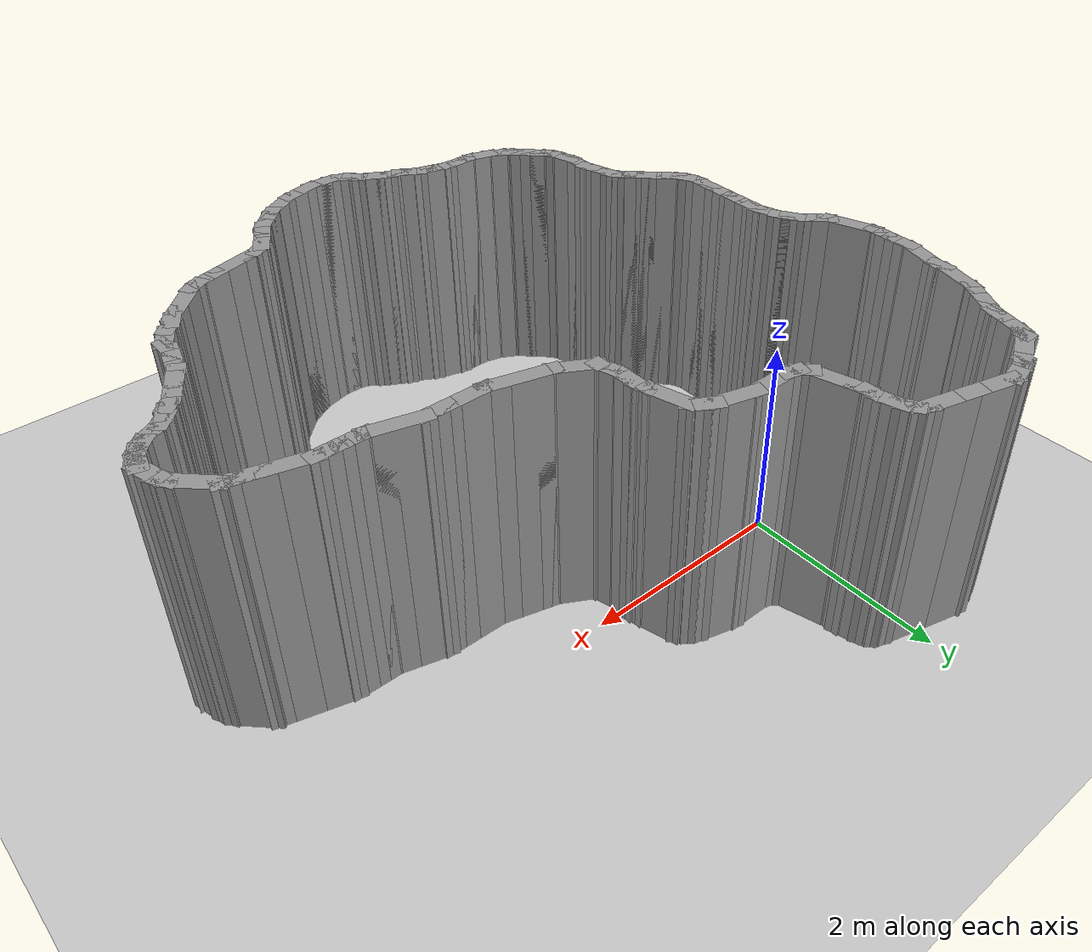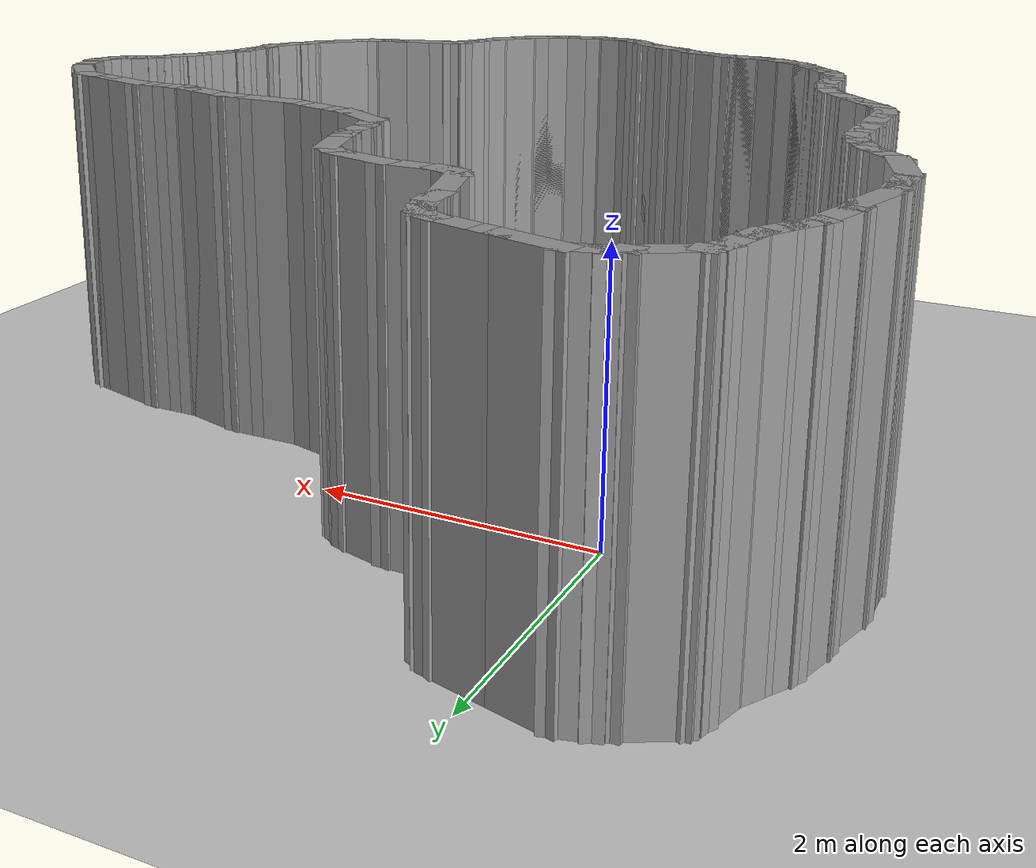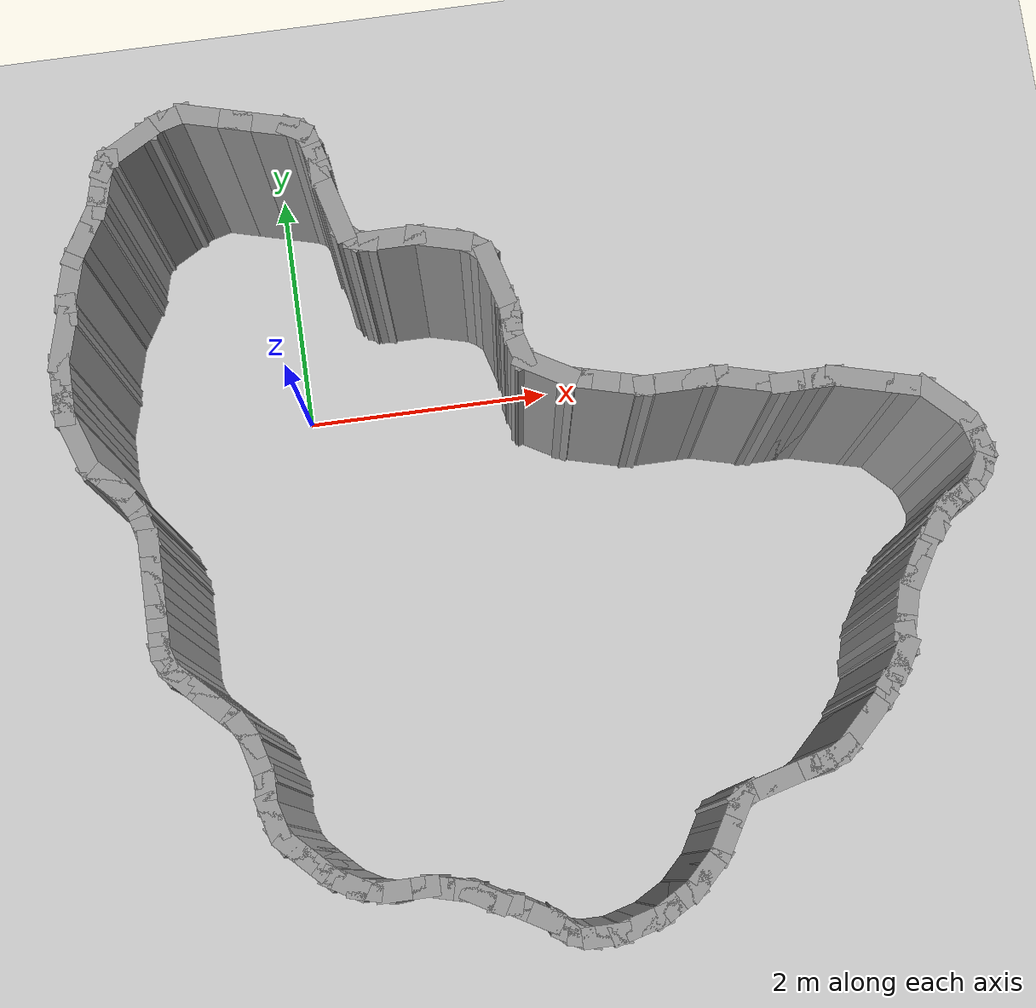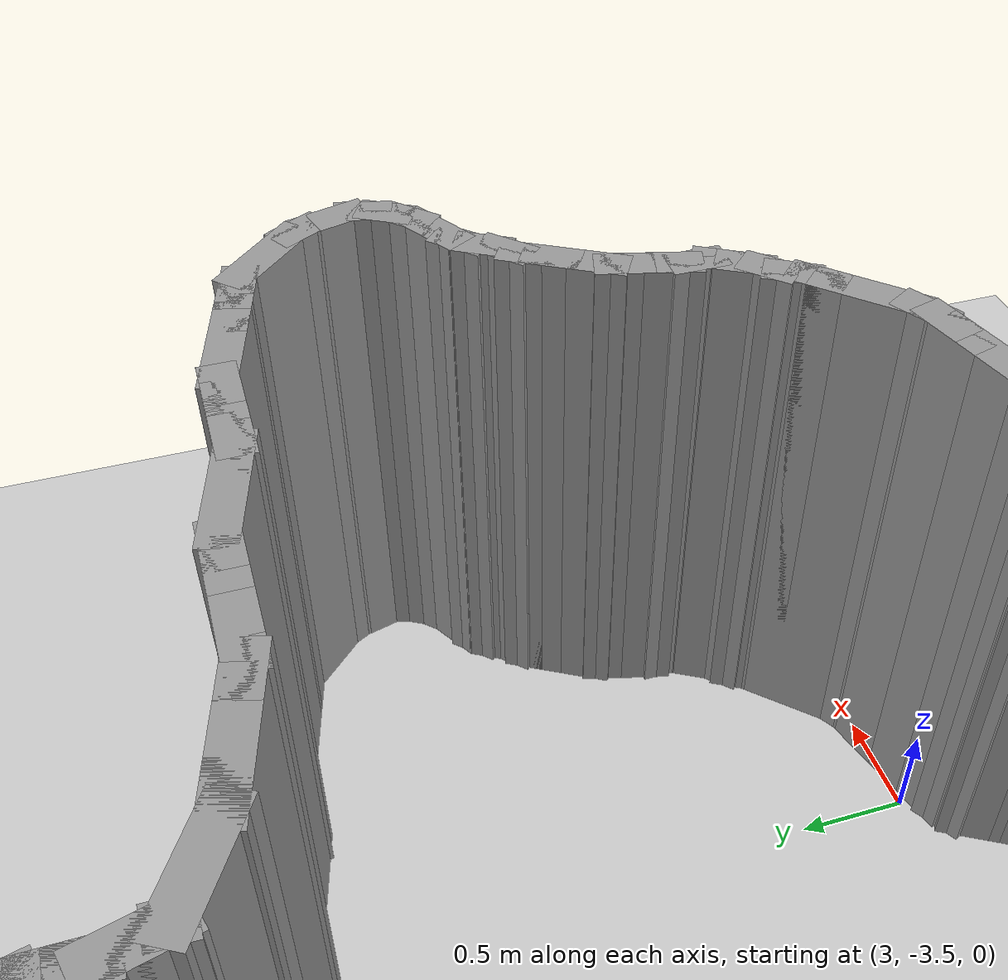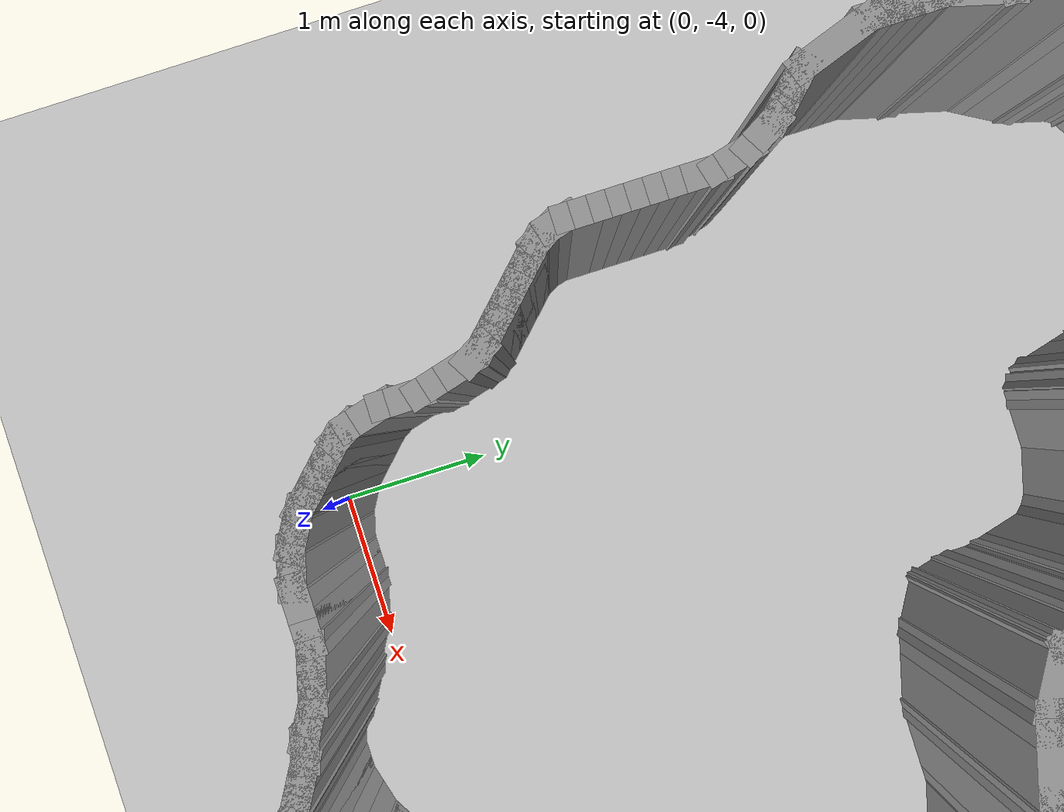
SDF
<sdf version="1.7">
 <world name="default">
  <light name="sun" type="directional">
   <pose>0 0 10 0 -0 0</pose>
   <diffuse>0.8 0.8 0.8 1</diffuse>
   <specular>0.2 0.2 0.2 1</specular>
   <attenuation>
    <range>1000</range>
    <constant>0.9</constant>
    <linear>0.01</linear>
    <quadratic>0.001</quadratic>
   </attenuation>
   <direction>-0.5 0.1 -0.9</direction>
   <spot><inner_angle>0</inner_angle><outer_angle>0</outer_angle><falloff>0</falloff></spot>
  </light>
  <model name="ground_plane">
   <static>1</static>
   <link name="link">
    <collision name="collision">
     <geometry><plane><normal>0 0 1</normal><size>100 100</size></plane></geometry>
     <surface>
      <contact><collide_bitmask>65535</collide_bitmask></contact>
      <friction><ode><mu>100</mu><mu2>50</mu2></ode></friction>
     </surface>
    </collision>
    <visual name="visual">
     <cast_shadows>0</cast_shadows>
     <geometry><plane><normal>0 0 1</normal><size>100 100</size></plane></geometry>
     <material>
      <script><uri>file://media/materials/scripts/gazebo.material</uri><name>Gazebo/Grey</name></script>
     </material>
    </visual>
   </link>
  </model>
  <gravity>0 0 -9.8</gravity>
  <magnetic_field>6e-06 2.3e-05 -4.2e-05</magnetic_field>
  <atmosphere type="adiabatic"/>
  <physics type="ode">
   <max_step_size>0.001</max_step_size>
   <real_time_factor>1</real_time_factor>
   <real_time_update_rate>1000</real_time_update_rate>
  </physics>
  <scene><ambient>0.4 0.4 0.4 1</ambient><background>0.7 0.7 0.7 1</background><shadows>1</shadows></scene>
  <spherical_coordinates>
   <surface_model>EARTH_WGS84</surface_model>
   <latitude_deg>0</latitude_deg>
   <longitude_deg>0</longitude_deg>
   <elevation>0</elevation>
   <heading_deg>0</heading_deg>
  </spherical_coordinates>
  <model name="pool11">
   <pose>1.69068 -1.09805 0 0 -0 0</pose>
   <link name="Wall_100">
    <collision name="Wall_100_Collision">
     <geometry><box><size>0.25 0.15 2.5</size></box></geometry>
     <pose>0 0 1.25 0 -0 0</pose>
    </collision>
    <visual name="Wall_100_Visual">
     <pose>0 0 1.25 0 -0 0</pose>
     <geometry><box><size>0.25 0.15 2.5</size></box></geometry>
     <material>
      <script><uri>file://media/materials/scripts/gazebo.material</uri><name>Gazebo/Grey</name></script>
      <ambient>1 1 1 1</ambient>
     </material>
     <meta><layer>0</layer></meta>
    </visual>
    <pose>2.29035 -1.96159 0 0 -0 1.0472</pose>
   </link>
   <link name="Wall_101">
    <collision name="Wall_101_Collision">
     <geometry><box><size>0.25 0.15 2.5</size></box></geometry>
     <pose>0 0 1.25 0 -0 0</pose>
    </collision>
    <visual name="Wall_101_Visual">
     <pose>0 0 1.25 0 -0 0</pose>
     <geometry><box><size>0.25 0.15 2.5</size></box></geometry>
     <material>
      <script><uri>file://media/materials/scripts/gazebo.material</uri><name>Gazebo/Grey</name></script>
      <ambient>1 1 1 1</ambient>
     </material>
     <meta><layer>0</layer></meta>
    </visual>
    <pose>2.35071 -1.88293 0 0 -0 0.785398</pose>
   </link>
   <link name="Wall_102">
    <collision name="Wall_102_Collision">
     <geometry><box><size>0.25 0.15 2.5</size></box></geometry>
     <pose>0 0 1.25 0 -0 0</pose>
    </collision>
    <visual name="Wall_102_Visual">
     <pose>0 0 1.25 0 -0 0</pose>
     <geometry><box><size>0.25 0.15 2.5</size></box></geometry>
     <material>
      <script><uri>file://media/materials/scripts/gazebo.material</uri><name>Gazebo/Grey</name></script>
      <ambient>1 1 1 1</ambient>
     </material>
     <meta><layer>0</layer></meta>
    </visual>
    <pose>2.41106 -1.80428 0 0 -0 1.0472</pose>
   </link>
   <link name="Wall_103">
    <collision name="Wall_103_Collision">
     <geometry><box><size>0.25 0.15 2.5</size></box></geometry>
     <pose>0 0 1.25 0 -0 0</pose>
    </collision>
    <visual name="Wall_103_Visual">
     <pose>0 0 1.25 0 -0 0</pose>
     <geometry><box><size>0.25 0.15 2.5</size></box></geometry>
     <material>
      <script><uri>file://media/materials/scripts/gazebo.material</uri><name>Gazebo/Grey</name></script>
      <ambient>1 1 1 1</ambient>
     </material>
     <meta><layer>0</layer></meta>
    </visual>
    <pose>2.46106 -1.71768 0 0 -0 1.0472</pose>
   </link>
   <link name="Wall_104">
    <collision name="Wall_104_Collision">
     <geometry><box><size>0.25 0.15 2.5</size></box></geometry>
     <pose>0 0 1.25 0 -0 0</pose>
    </collision>
    <visual name="Wall_104_Visual">
     <pose>0 0 1.25 0 -0 0</pose>
     <geometry><box><size>0.25 0.15 2.5</size></box></geometry>
     <material>
      <script><uri>file://media/materials/scripts/gazebo.material</uri><name>Gazebo/Grey</name></script>
      <ambient>1 1 1 1</ambient>
     </material>
     <meta><layer>0</layer></meta>
    </visual>
    <pose>2.48606 -1.62437 0 0 -0 1.5708</pose>
   </link>
   <link name="Wall_105">
    <collision name="Wall_105_Collision">
     <geometry><box><size>0.25 0.15 2.5</size></box></geometry>
     <pose>0 0 1.25 0 -0 0</pose>
    </collision>
    <visual name="Wall_105_Visual">
     <pose>0 0 1.25 0 -0 0</pose>
     <geometry><box><size>0.25 0.15 2.5</size></box></geometry>
     <material>
      <script><uri>file://media/materials/scripts/gazebo.material</uri><name>Gazebo/Grey</name></script>
      <ambient>1 1 1 1</ambient>
     </material>
     <meta><layer>0</layer></meta>
    </visual>
    <pose>2.499 -1.52608 0 0 -0 1.309</pose>
   </link>
   <link name="Wall_106">
    <collision name="Wall_106_Collision">
     <geometry><box><size>0.25 0.15 2.5</size></box></geometry>
     <pose>0 0 1.25 0 -0 0</pose>
    </collision>
    <visual name="Wall_106_Visual">
     <pose>0 0 1.25 0 -0 0</pose>
     <geometry><box><size>0.25 0.15 2.5</size></box></geometry>
     <material>
      <script><uri>file://media/materials/scripts/gazebo.material</uri><name>Gazebo/Grey</name></script>
      <ambient>1 1 1 1</ambient>
     </material>
     <meta><layer>0</layer></meta>
    </visual>
    <pose>2.52489 -1.42948 0 0 -0 1.309</pose>
   </link>
   <link name="Wall_107">
    <collision name="Wall_107_Collision">
     <geometry><box><size>0.25 0.15 2.5</size></box></geometry>
     <pose>0 0 1.25 0 -0 0</pose>
    </collision>
    <visual name="Wall_107_Visual">
     <pose>0 0 1.25 0 -0 0</pose>
     <geometry><box><size>0.25 0.15 2.5</size></box></geometry>
     <material>
      <script><uri>file://media/materials/scripts/gazebo.material</uri><name>Gazebo/Grey</name></script>
      <ambient>1 1 1 1</ambient>
     </material>
     <meta><layer>0</layer></meta>
    </visual>
    <pose>2.55077 -1.33289 0 0 -0 1.309</pose>
   </link>
   <link name="Wall_108">
    <collision name="Wall_108_Collision">
     <geometry><box><size>0.25 0.15 2.5</size></box></geometry>
     <pose>0 0 1.25 0 -0 0</pose>
    </collision>
    <visual name="Wall_108_Visual">
     <pose>0 0 1.25 0 -0 0</pose>
     <geometry><box><size>0.25 0.15 2.5</size></box></geometry>
     <material>
      <script><uri>file://media/materials/scripts/gazebo.material</uri><name>Gazebo/Grey</name></script>
      <ambient>1 1 1 1</ambient>
     </material>
     <meta><layer>0</layer></meta>
    </visual>
    <pose>2.58871 -1.24129 0 0 -0 1.0472</pose>
   </link>
   <link name="Wall_109">
    <collision name="Wall_109_Collision">
     <geometry><box><size>0.25 0.15 2.5</size></box></geometry>
     <pose>0 0 1.25 0 -0 0</pose>
    </collision>
    <visual name="Wall_109_Visual">
     <pose>0 0 1.25 0 -0 0</pose>
     <geometry><box><size>0.25 0.15 2.5</size></box></geometry>
     <material>
      <script><uri>file://media/materials/scripts/gazebo.material</uri><name>Gazebo/Grey</name></script>
      <ambient>1 1 1 1</ambient>
     </material>
     <meta><layer>0</layer></meta>
    </visual>
    <pose>2.63871 -1.15469 0 0 -0 1.0472</pose>
   </link>
   <link name="Wall_110">
    <collision name="Wall_110_Collision">
     <geometry><box><size>0.25 0.15 2.5</size></box></geometry>
     <pose>0 0 1.25 0 -0 0</pose>
    </collision>
    <visual name="Wall_110_Visual">
     <pose>0 0 1.25 0 -0 0</pose>
     <geometry><box><size>0.25 0.15 2.5</size></box></geometry>
     <material>
      <script><uri>file://media/materials/scripts/gazebo.material</uri><name>Gazebo/Grey</name></script>
      <ambient>1 1 1 1</ambient>
     </material>
     <meta><layer>0</layer></meta>
    </visual>
    <pose>2.68871 -1.06809 0 0 -0 1.0472</pose>
   </link>
   <link name="Wall_111">
    <collision name="Wall_111_Collision">
     <geometry><box><size>0.25 0.15 2.5</size></box></geometry>
     <pose>0 0 1.25 0 -0 0</pose>
    </collision>
    <visual name="Wall_111_Visual">
     <pose>0 0 1.25 0 -0 0</pose>
     <geometry><box><size>0.25 0.15 2.5</size></box></geometry>
     <material>
      <script><uri>file://media/materials/scripts/gazebo.material</uri><name>Gazebo/Grey</name></script>
      <ambient>1 1 1 1</ambient>
     </material>
     <meta><layer>0</layer></meta>
    </visual>
    <pose>2.73871 -0.981487 0 0 -0 1.0472</pose>
   </link>
   <link name="Wall_112">
    <collision name="Wall_112_Collision">
     <geometry><box><size>0.25 0.15 2.5</size></box></geometry>
     <pose>0 0 1.25 0 -0 0</pose>
    </collision>
    <visual name="Wall_112_Visual">
     <pose>0 0 1.25 0 -0 0</pose>
     <geometry><box><size>0.25 0.15 2.5</size></box></geometry>
     <material>
      <script><uri>file://media/materials/scripts/gazebo.material</uri><name>Gazebo/Grey</name></script>
      <ambient>1 1 1 1</ambient>
     </material>
     <meta><layer>0</layer></meta>
    </visual>
    <pose>2.79907 -0.90283 0 0 -0 0.785398</pose>
   </link>
   <link name="Wall_113">
    <collision name="Wall_113_Collision">
     <geometry><box><size>0.25 0.15 2.5</size></box></geometry>
     <pose>0 0 1.25 0 -0 0</pose>
    </collision>
    <visual name="Wall_113_Visual">
     <pose>0 0 1.25 0 -0 0</pose>
     <geometry><box><size>0.25 0.15 2.5</size></box></geometry>
     <material>
      <script><uri>file://media/materials/scripts/gazebo.material</uri><name>Gazebo/Grey</name></script>
      <ambient>1 1 1 1</ambient>
     </material>
     <meta><layer>0</layer></meta>
    </visual>
    <pose>2.85942 -0.824173 0 0 -0 1.0472</pose>
   </link>
   <link name="Wall_114">
    <collision name="Wall_114_Collision">
     <geometry><box><size>0.25 0.15 2.5</size></box></geometry>
     <pose>0 0 1.25 0 -0 0</pose>
    </collision>
    <visual name="Wall_114_Visual">
     <pose>0 0 1.25 0 -0 0</pose>
     <geometry><box><size>0.25 0.15 2.5</size></box></geometry>
     <material>
      <script><uri>file://media/materials/scripts/gazebo.material</uri><name>Gazebo/Grey</name></script>
      <ambient>1 1 1 1</ambient>
     </material>
     <meta><layer>0</layer></meta>
    </visual>
    <pose>2.91978 -0.745517 0 0 -0 0.785398</pose>
   </link>
   <link name="Wall_115">
    <collision name="Wall_115_Collision">
     <geometry><box><size>0.25 0.15 2.5</size></box></geometry>
     <pose>0 0 1.25 0 -0 0</pose>
    </collision>
    <visual name="Wall_115_Visual">
     <pose>0 0 1.25 0 -0 0</pose>
     <geometry><box><size>0.25 0.15 2.5</size></box></geometry>
     <material>
      <script><uri>file://media/materials/scripts/gazebo.material</uri><name>Gazebo/Grey</name></script>
      <ambient>1 1 1 1</ambient>
     </material>
     <meta><layer>0</layer></meta>
    </visual>
    <pose>2.99843 -0.685162 0 0 -0 0.523599</pose>
   </link>
   <link name="Wall_116">
    <collision name="Wall_116_Collision">
     <geometry><box><size>0.25 0.15 2.5</size></box></geometry>
     <pose>0 0 1.25 0 -0 0</pose>
    </collision>
    <visual name="Wall_116_Visual">
     <pose>0 0 1.25 0 -0 0</pose>
     <geometry><box><size>0.25 0.15 2.5</size></box></geometry>
     <material>
      <script><uri>file://media/materials/scripts/gazebo.material</uri><name>Gazebo/Grey</name></script>
      <ambient>1 1 1 1</ambient>
     </material>
     <meta><layer>0</layer></meta>
    </visual>
    <pose>3.08503 -0.635162 0 0 -0 0.523599</pose>
   </link>
   <link name="Wall_117">
    <collision name="Wall_117_Collision">
     <geometry><box><size>0.25 0.15 2.5</size></box></geometry>
     <pose>0 0 1.25 0 -0 0</pose>
    </collision>
    <visual name="Wall_117_Visual">
     <pose>0 0 1.25 0 -0 0</pose>
     <geometry><box><size>0.25 0.15 2.5</size></box></geometry>
     <material>
      <script><uri>file://media/materials/scripts/gazebo.material</uri><name>Gazebo/Grey</name></script>
      <ambient>1 1 1 1</ambient>
     </material>
     <meta><layer>0</layer></meta>
    </visual>
    <pose>3.16369 -0.574806 0 0 -0 0.785398</pose>
   </link>
   <link name="Wall_118">
    <collision name="Wall_118_Collision">
     <geometry><box><size>0.25 0.15 2.5</size></box></geometry>
     <pose>0 0 1.25 0 -0 0</pose>
    </collision>
    <visual name="Wall_118_Visual">
     <pose>0 0 1.25 0 -0 0</pose>
     <geometry><box><size>0.25 0.15 2.5</size></box></geometry>
     <material>
      <script><uri>file://media/materials/scripts/gazebo.material</uri><name>Gazebo/Grey</name></script>
      <ambient>1 1 1 1</ambient>
     </material>
     <meta><layer>0</layer></meta>
    </visual>
    <pose>3.22405 -0.49615 0 0 -0 1.0472</pose>
   </link>
   <link name="Wall_119">
    <collision name="Wall_119_Collision">
     <geometry><box><size>0.25 0.15 2.5</size></box></geometry>
     <pose>0 0 1.25 0 -0 0</pose>
    </collision>
    <visual name="Wall_119_Visual">
     <pose>0 0 1.25 0 -0 0</pose>
     <geometry><box><size>0.25 0.15 2.5</size></box></geometry>
     <material>
      <script><uri>file://media/materials/scripts/gazebo.material</uri><name>Gazebo/Grey</name></script>
      <ambient>1 1 1 1</ambient>
     </material>
     <meta><layer>0</layer></meta>
    </visual>
    <pose>3.26199 -0.404552 0 0 -0 1.309</pose>
   </link>
   <link name="Wall_120">
    <collision name="Wall_120_Collision">
     <geometry><box><size>0.25 0.15 2.5</size></box></geometry>
     <pose>0 0 1.25 0 -0 0</pose>
    </collision>
    <visual name="Wall_120_Visual">
     <pose>0 0 1.25 0 -0 0</pose>
     <geometry><box><size>0.25 0.15 2.5</size></box></geometry>
     <material>
      <script><uri>file://media/materials/scripts/gazebo.material</uri><name>Gazebo/Grey</name></script>
      <ambient>1 1 1 1</ambient>
     </material>
     <meta><layer>0</layer></meta>
    </visual>
    <pose>3.26199 -0.30796 0 0 -0 1.8326</pose>
   </link>
   <link name="Wall_121">
    <collision name="Wall_121_Collision">
     <geometry><box><size>0.25 0.15 2.5</size></box></geometry>
     <pose>0 0 1.25 0 -0 0</pose>
    </collision>
    <visual name="Wall_121_Visual">
     <pose>0 0 1.25 0 -0 0</pose>
     <geometry><box><size>0.25 0.15 2.5</size></box></geometry>
     <material>
      <script><uri>file://media/materials/scripts/gazebo.material</uri><name>Gazebo/Grey</name></script>
      <ambient>1 1 1 1</ambient>
     </material>
     <meta><layer>0</layer></meta>
    </visual>
    <pose>3.23611 -0.211367 0 0 -0 1.8326</pose>
   </link>
   <link name="Wall_122">
    <collision name="Wall_122_Collision">
     <geometry><box><size>0.25 0.15 2.5</size></box></geometry>
     <pose>0 0 1.25 0 -0 0</pose>
    </collision>
    <visual name="Wall_122_Visual">
     <pose>0 0 1.25 0 -0 0</pose>
     <geometry><box><size>0.25 0.15 2.5</size></box></geometry>
     <material>
      <script><uri>file://media/materials/scripts/gazebo.material</uri><name>Gazebo/Grey</name></script>
      <ambient>1 1 1 1</ambient>
     </material>
     <meta><layer>0</layer></meta>
    </visual>
    <pose>3.19816 -0.119769 0 0 -0 2.0944</pose>
   </link>
   <link name="Wall_123">
    <collision name="Wall_123_Collision">
     <geometry><box><size>0.5 0.15 2.5</size></box></geometry>
     <pose>0 0 1.25 0 -0 0</pose>
    </collision>
    <visual name="Wall_123_Visual">
     <pose>0 0 1.25 0 -0 0</pose>
     <geometry><box><size>0.5 0.15 2.5</size></box></geometry>
     <material>
      <script><uri>file://media/materials/scripts/gazebo.material</uri><name>Gazebo/Grey</name></script>
      <ambient>1 1 1 1</ambient>
     </material>
     <meta><layer>0</layer></meta>
    </visual>
    <pose>3.04942 0.047276 0 0 -0 2.35619</pose>
   </link>
   <link name="Wall_124">
    <collision name="Wall_124_Collision">
     <geometry><box><size>0.25 0.15 2.5</size></box></geometry>
     <pose>0 0 1.25 0 -0 0</pose>
    </collision>
    <visual name="Wall_124_Visual">
     <pose>0 0 1.25 0 -0 0</pose>
     <geometry><box><size>0.25 0.15 2.5</size></box></geometry>
     <material>
      <script><uri>file://media/materials/scripts/gazebo.material</uri><name>Gazebo/Grey</name></script>
      <ambient>1 1 1 1</ambient>
     </material>
     <meta><layer>0</layer></meta>
    </visual>
    <pose>2.87738 0.18396 0 0 -0 2.87979</pose>
   </link>
   <link name="Wall_125">
    <collision name="Wall_125_Collision">
     <geometry><box><size>0.25 0.15 2.5</size></box></geometry>
     <pose>0 0 1.25 0 -0 0</pose>
    </collision>
    <visual name="Wall_125_Visual">
     <pose>0 0 1.25 0 -0 0</pose>
     <geometry><box><size>0.25 0.15 2.5</size></box></geometry>
     <material>
      <script><uri>file://media/materials/scripts/gazebo.material</uri><name>Gazebo/Grey</name></script>
      <ambient>1 1 1 1</ambient>
     </material>
     <meta><layer>0</layer></meta>
    </visual>
    <pose>2.78079 0.209842 0 0 -0 2.87979</pose>
   </link>
   <link name="Wall_126">
    <collision name="Wall_126_Collision">
     <geometry><box><size>0.25 0.15 2.5</size></box></geometry>
     <pose>0 0 1.25 0 -0 0</pose>
    </collision>
    <visual name="Wall_126_Visual">
     <pose>0 0 1.25 0 -0 0</pose>
     <geometry><box><size>0.25 0.15 2.5</size></box></geometry>
     <material>
      <script><uri>file://media/materials/scripts/gazebo.material</uri><name>Gazebo/Grey</name></script>
      <ambient>1 1 1 1</ambient>
     </material>
     <meta><layer>0</layer></meta>
    </visual>
    <pose>2.6842 0.235724 0 0 -0 2.87979</pose>
   </link>
   <link name="Wall_127">
    <collision name="Wall_127_Collision">
     <geometry><box><size>0.5 0.15 2.5</size></box></geometry>
     <pose>0 0 1.25 0 -0 0</pose>
    </collision>
    <visual name="Wall_127_Visual">
     <pose>0 0 1.25 0 -0 0</pose>
     <geometry><box><size>0.5 0.15 2.5</size></box></geometry>
     <material>
      <script><uri>file://media/materials/scripts/gazebo.material</uri><name>Gazebo/Grey</name></script>
      <ambient>1 1 1 1</ambient>
     </material>
     <meta><layer>0</layer></meta>
    </visual>
    <pose>2.46686 0.293958 0 0 -0 2.87979</pose>
   </link>
   <link name="Wall_128">
    <collision name="Wall_128_Collision">
     <geometry><box><size>0.25 0.15 2.5</size></box></geometry>
     <pose>0 0 1.25 0 -0 0</pose>
    </collision>
    <visual name="Wall_128_Visual">
     <pose>0 0 1.25 0 -0 0</pose>
     <geometry><box><size>0.25 0.15 2.5</size></box></geometry>
     <material>
      <script><uri>file://media/materials/scripts/gazebo.material</uri><name>Gazebo/Grey</name></script>
      <ambient>1 1 1 1</ambient>
     </material>
     <meta><layer>0</layer></meta>
    </visual>
    <pose>2.24783 0.339252 0 0 -0 3.14159</pose>
   </link>
   <link name="Wall_129">
    <collision name="Wall_129_Collision">
     <geometry><box><size>0.25 0.15 2.5</size></box></geometry>
     <pose>0 0 1.25 0 -0 0</pose>
    </collision>
    <visual name="Wall_129_Visual">
     <pose>0 0 1.25 0 -0 0</pose>
     <geometry><box><size>0.25 0.15 2.5</size></box></geometry>
     <material>
      <script><uri>file://media/materials/scripts/gazebo.material</uri><name>Gazebo/Grey</name></script>
      <ambient>1 1 1 1</ambient>
     </material>
     <meta><layer>0</layer></meta>
    </visual>
    <pose>2.14783 0.339252 0 0 -0 3.14159</pose>
   </link>
   <link name="Wall_130">
    <collision name="Wall_130_Collision">
     <geometry><box><size>0.25 0.15 2.5</size></box></geometry>
     <pose>0 0 1.25 0 -0 0</pose>
    </collision>
    <visual name="Wall_130_Visual">
     <pose>0 0 1.25 0 -0 0</pose>
     <geometry><box><size>0.25 0.15 2.5</size></box></geometry>
     <material>
      <script><uri>file://media/materials/scripts/gazebo.material</uri><name>Gazebo/Grey</name></script>
      <ambient>1 1 1 1</ambient>
     </material>
     <meta><layer>0</layer></meta>
    </visual>
    <pose>2.04783 0.339252 0 0 -0 3.14159</pose>
   </link>
   <link name="Wall_131">
    <collision name="Wall_131_Collision">
     <geometry><box><size>0.25 0.15 2.5</size></box></geometry>
     <pose>0 0 1.25 0 -0 0</pose>
    </collision>
    <visual name="Wall_131_Visual">
     <pose>0 0 1.25 0 -0 0</pose>
     <geometry><box><size>0.25 0.15 2.5</size></box></geometry>
     <material>
      <script><uri>file://media/materials/scripts/gazebo.material</uri><name>Gazebo/Grey</name></script>
      <ambient>1 1 1 1</ambient>
     </material>
     <meta><layer>0</layer></meta>
    </visual>
    <pose>1.94783 0.339252 0 0 -0 3.14159</pose>
   </link>
   <link name="Wall_132">
    <collision name="Wall_132_Collision">
     <geometry><box><size>0.25 0.15 2.5</size></box></geometry>
     <pose>0 0 1.25 0 -0 0</pose>
    </collision>
    <visual name="Wall_132_Visual">
     <pose>0 0 1.25 0 -0 0</pose>
     <geometry><box><size>0.25 0.15 2.5</size></box></geometry>
     <material>
      <script><uri>file://media/materials/scripts/gazebo.material</uri><name>Gazebo/Grey</name></script>
      <ambient>1 1 1 1</ambient>
     </material>
     <meta><layer>0</layer></meta>
    </visual>
    <pose>1.84953 0.352193 0 0 -0 2.87979</pose>
   </link>
   <link name="Wall_133">
    <collision name="Wall_133_Collision">
     <geometry><box><size>0.5 0.15 2.5</size></box></geometry>
     <pose>0 0 1.25 0 -0 0</pose>
    </collision>
    <visual name="Wall_133_Visual">
     <pose>0 0 1.25 0 -0 0</pose>
     <geometry><box><size>0.5 0.15 2.5</size></box></geometry>
     <material>
      <script><uri>file://media/materials/scripts/gazebo.material</uri><name>Gazebo/Grey</name></script>
      <ambient>1 1 1 1</ambient>
     </material>
     <meta><layer>0</layer></meta>
    </visual>
    <pose>1.6322 0.410427 0 0 -0 2.87979</pose>
   </link>
   <link name="Wall_134">
    <collision name="Wall_134_Collision">
     <geometry><box><size>0.25 0.15 2.5</size></box></geometry>
     <pose>0 0 1.25 0 -0 0</pose>
    </collision>
    <visual name="Wall_134_Visual">
     <pose>0 0 1.25 0 -0 0</pose>
     <geometry><box><size>0.25 0.15 2.5</size></box></geometry>
     <material>
      <script><uri>file://media/materials/scripts/gazebo.material</uri><name>Gazebo/Grey</name></script>
      <ambient>1 1 1 1</ambient>
     </material>
     <meta><layer>0</layer></meta>
    </visual>
    <pose>1.41316 0.45572 0 0 -0 3.14159</pose>
   </link>
   <link name="Wall_135">
    <collision name="Wall_135_Collision">
     <geometry><box><size>0.25 0.15 2.5</size></box></geometry>
     <pose>0 0 1.25 0 -0 0</pose>
    </collision>
    <visual name="Wall_135_Visual">
     <pose>0 0 1.25 0 -0 0</pose>
     <geometry><box><size>0.25 0.15 2.5</size></box></geometry>
     <material>
      <script><uri>file://media/materials/scripts/gazebo.material</uri><name>Gazebo/Grey</name></script>
      <ambient>1 1 1 1</ambient>
     </material>
     <meta><layer>0</layer></meta>
    </visual>
    <pose>1.31316 0.45572 0 0 -0 3.14159</pose>
   </link>
   <link name="Wall_136">
    <collision name="Wall_136_Collision">
     <geometry><box><size>0.5 0.15 2.5</size></box></geometry>
     <pose>0 0 1.25 0 -0 0</pose>
    </collision>
    <visual name="Wall_136_Visual">
     <pose>0 0 1.25 0 -0 0</pose>
     <geometry><box><size>0.5 0.15 2.5</size></box></geometry>
     <material>
      <script><uri>file://media/materials/scripts/gazebo.material</uri><name>Gazebo/Grey</name></script>
      <ambient>1 1 1 1</ambient>
     </material>
     <meta><layer>0</layer></meta>
    </visual>
    <pose>1.08816 0.45572 0 0 -0 3.14159</pose>
   </link>
   <link name="Wall_137">
    <collision name="Wall_137_Collision">
     <geometry><box><size>0.15 0.15 2.5</size></box></geometry>
     <pose>0 0 1.25 0 -0 0</pose>
    </collision>
    <visual name="Wall_137_Visual">
     <pose>0 0 1.25 0 -0 0</pose>
     <geometry><box><size>0.15 0.15 2.5</size></box></geometry>
     <material>
      <script><uri>file://media/materials/scripts/gazebo.material</uri><name>Gazebo/Grey</name></script>
      <ambient>1 1 1 1</ambient>
     </material>
     <meta><layer>0</layer></meta>
    </visual>
    <pose>0.913159 0.45572 0 0 -0 0</pose>
   </link>
   <link name="Wall_138">
    <collision name="Wall_138_Collision">
     <geometry><box><size>0.25 0.15 2.5</size></box></geometry>
     <pose>0 0 1.25 0 -0 0</pose>
    </collision>
    <visual name="Wall_138_Visual">
     <pose>0 0 1.25 0 -0 0</pose>
     <geometry><box><size>0.25 0.15 2.5</size></box></geometry>
     <material>
      <script><uri>file://media/materials/scripts/gazebo.material</uri><name>Gazebo/Grey</name></script>
      <ambient>1 1 1 1</ambient>
     </material>
     <meta><layer>0</layer></meta>
    </visual>
    <pose>0.864863 0.468661 0 0 -0 2.87979</pose>
   </link>
   <link name="Wall_139">
    <collision name="Wall_139_Collision">
     <geometry><box><size>0.5 0.15 2.5</size></box></geometry>
     <pose>0 0 1.25 0 -0 0</pose>
    </collision>
    <visual name="Wall_139_Visual">
     <pose>0 0 1.25 0 -0 0</pose>
     <geometry><box><size>0.5 0.15 2.5</size></box></geometry>
     <material>
      <script><uri>file://media/materials/scripts/gazebo.material</uri><name>Gazebo/Grey</name></script>
      <ambient>1 1 1 1</ambient>
     </material>
     <meta><layer>0</layer></meta>
    </visual>
    <pose>0.647529 0.526895 0 0 -0 2.87979</pose>
   </link>
   <link name="Wall_140">
    <collision name="Wall_140_Collision">
     <geometry><box><size>0.25 0.15 2.5</size></box></geometry>
     <pose>0 0 1.25 0 -0 0</pose>
    </collision>
    <visual name="Wall_140_Visual">
     <pose>0 0 1.25 0 -0 0</pose>
     <geometry><box><size>0.25 0.15 2.5</size></box></geometry>
     <material>
      <script><uri>file://media/materials/scripts/gazebo.material</uri><name>Gazebo/Grey</name></script>
      <ambient>1 1 1 1</ambient>
     </material>
     <meta><layer>0</layer></meta>
    </visual>
    <pose>0.430196 0.58513 0 0 -0 2.87979</pose>
   </link>
   <link name="Wall_141">
    <collision name="Wall_141_Collision">
     <geometry><box><size>0.5 0.15 2.5</size></box></geometry>
     <pose>0 0 1.25 0 -0 0</pose>
    </collision>
    <visual name="Wall_141_Visual">
     <pose>0 0 1.25 0 -0 0</pose>
     <geometry><box><size>0.5 0.15 2.5</size></box></geometry>
     <material>
      <script><uri>file://media/materials/scripts/gazebo.material</uri><name>Gazebo/Grey</name></script>
      <ambient>1 1 1 1</ambient>
     </material>
     <meta><layer>0</layer></meta>
    </visual>
    <pose>0.230345 0.685571 0 0 -0 2.61799</pose>
   </link>
   <link name="Wall_142">
    <collision name="Wall_142_Collision">
     <geometry><box><size>0.15 0.15 2.5</size></box></geometry>
     <pose>0 0 1.25 0 -0 0</pose>
    </collision>
    <visual name="Wall_142_Visual">
     <pose>0 0 1.25 0 -0 0</pose>
     <geometry><box><size>0.15 0.15 2.5</size></box></geometry>
     <material>
      <script><uri>file://media/materials/scripts/gazebo.material</uri><name>Gazebo/Grey</name></script>
      <ambient>1 1 1 1</ambient>
     </material>
     <meta><layer>0</layer></meta>
    </visual>
    <pose>0.078791 0.773071 0 0 -0 0</pose>
   </link>
   <link name="Wall_143">
    <collision name="Wall_143_Collision">
     <geometry><box><size>0.25 0.15 2.5</size></box></geometry>
     <pose>0 0 1.25 0 -0 0</pose>
    </collision>
    <visual name="Wall_143_Visual">
     <pose>0 0 1.25 0 -0 0</pose>
     <geometry><box><size>0.25 0.15 2.5</size></box></geometry>
     <material>
      <script><uri>file://media/materials/scripts/gazebo.material</uri><name>Gazebo/Grey</name></script>
      <ambient>1 1 1 1</ambient>
     </material>
     <meta><layer>0</layer></meta>
    </visual>
    <pose>0.06585 0.821367 0 0 -0 1.8326</pose>
   </link>
   <link name="Wall_144">
    <collision name="Wall_144_Collision">
     <geometry><box><size>0.25 0.15 2.5</size></box></geometry>
     <pose>0 0 1.25 0 -0 0</pose>
    </collision>
    <visual name="Wall_144_Visual">
     <pose>0 0 1.25 0 -0 0</pose>
     <geometry><box><size>0.25 0.15 2.5</size></box></geometry>
     <material>
      <script><uri>file://media/materials/scripts/gazebo.material</uri><name>Gazebo/Grey</name></script>
      <ambient>1 1 1 1</ambient>
     </material>
     <meta><layer>0</layer></meta>
    </visual>
    <pose>0.039968 0.917959 0 0 -0 1.8326</pose>
   </link>
   <link name="Wall_145">
    <collision name="Wall_145_Collision">
     <geometry><box><size>0.25 0.15 2.5</size></box></geometry>
     <pose>0 0 1.25 0 -0 0</pose>
    </collision>
    <visual name="Wall_145_Visual">
     <pose>0 0 1.25 0 -0 0</pose>
     <geometry><box><size>0.25 0.15 2.5</size></box></geometry>
     <material>
      <script><uri>file://media/materials/scripts/gazebo.material</uri><name>Gazebo/Grey</name></script>
      <ambient>1 1 1 1</ambient>
     </material>
     <meta><layer>0</layer></meta>
    </visual>
    <pose>0.027027 1.01626 0 0 -0 1.5708</pose>
   </link>
   <link name="Wall_146">
    <collision name="Wall_146_Collision">
     <geometry><box><size>0.25 0.15 2.5</size></box></geometry>
     <pose>0 0 1.25 0 -0 0</pose>
    </collision>
    <visual name="Wall_146_Visual">
     <pose>0 0 1.25 0 -0 0</pose>
     <geometry><box><size>0.25 0.15 2.5</size></box></geometry>
     <material>
      <script><uri>file://media/materials/scripts/gazebo.material</uri><name>Gazebo/Grey</name></script>
      <ambient>1 1 1 1</ambient>
     </material>
     <meta><layer>0</layer></meta>
    </visual>
    <pose>0.027027 1.11626 0 0 -0 1.5708</pose>
   </link>
   <link name="Wall_147">
    <collision name="Wall_147_Collision">
     <geometry><box><size>0.15 0.15 2.5</size></box></geometry>
     <pose>0 0 1.25 0 -0 0</pose>
    </collision>
    <visual name="Wall_147_Visual">
     <pose>0 0 1.25 0 -0 0</pose>
     <geometry><box><size>0.15 0.15 2.5</size></box></geometry>
     <material>
      <script><uri>file://media/materials/scripts/gazebo.material</uri><name>Gazebo/Grey</name></script>
      <ambient>1 1 1 1</ambient>
     </material>
     <meta><layer>0</layer></meta>
    </visual>
    <pose>0.027027 1.16626 0 0 -0 0</pose>
   </link>
   <link name="Wall_148">
    <collision name="Wall_148_Collision">
     <geometry><box><size>0.25 0.15 2.5</size></box></geometry>
     <pose>0 0 1.25 0 -0 0</pose>
    </collision>
    <visual name="Wall_148_Visual">
     <pose>0 0 1.25 0 -0 0</pose>
     <geometry><box><size>0.25 0.15 2.5</size></box></geometry>
     <material>
      <script><uri>file://media/materials/scripts/gazebo.material</uri><name>Gazebo/Grey</name></script>
      <ambient>1 1 1 1</ambient>
     </material>
     <meta><layer>0</layer></meta>
    </visual>
    <pose>0.014086 1.21455 0 0 -0 1.8326</pose>
   </link>
   <link name="Wall_149">
    <collision name="Wall_149_Collision">
     <geometry><box><size>0.15 0.15 2.5</size></box></geometry>
     <pose>0 0 1.25 0 -0 0</pose>
    </collision>
    <visual name="Wall_149_Visual">
     <pose>0 0 1.25 0 -0 0</pose>
     <geometry><box><size>0.15 0.15 2.5</size></box></geometry>
     <material>
      <script><uri>file://media/materials/scripts/gazebo.material</uri><name>Gazebo/Grey</name></script>
      <ambient>1 1 1 1</ambient>
     </material>
     <meta><layer>0</layer></meta>
    </visual>
    <pose>0.001145 1.26285 0 0 -0 0</pose>
   </link>
   <link name="Wall_150">
    <collision name="Wall_150_Collision">
     <geometry><box><size>0.5 0.15 2.5</size></box></geometry>
     <pose>0 0 1.25 0 -0 0</pose>
    </collision>
    <visual name="Wall_150_Visual">
     <pose>0 0 1.25 0 -0 0</pose>
     <geometry><box><size>0.5 0.15 2.5</size></box></geometry>
     <material>
      <script><uri>file://media/materials/scripts/gazebo.material</uri><name>Gazebo/Grey</name></script>
      <ambient>1 1 1 1</ambient>
     </material>
     <meta><layer>0</layer></meta>
    </visual>
    <pose>-0.044148 1.43189 0 0 -0 1.8326</pose>
   </link>
   <link name="Wall_151">
    <collision name="Wall_151_Collision">
     <geometry><box><size>0.25 0.15 2.5</size></box></geometry>
     <pose>0 0 1.25 0 -0 0</pose>
    </collision>
    <visual name="Wall_151_Visual">
     <pose>0 0 1.25 0 -0 0</pose>
     <geometry><box><size>0.25 0.15 2.5</size></box></geometry>
     <material>
      <script><uri>file://media/materials/scripts/gazebo.material</uri><name>Gazebo/Grey</name></script>
      <ambient>1 1 1 1</ambient>
     </material>
     <meta><layer>0</layer></meta>
    </visual>
    <pose>-0.124797 1.63628 0 0 -0 2.35619</pose>
   </link>
   <link name="Wall_152">
    <collision name="Wall_152_Collision">
     <geometry><box><size>0.25 0.15 2.5</size></box></geometry>
     <pose>0 0 1.25 0 -0 0</pose>
    </collision>
    <visual name="Wall_152_Visual">
     <pose>0 0 1.25 0 -0 0</pose>
     <geometry><box><size>0.25 0.15 2.5</size></box></geometry>
     <material>
      <script><uri>file://media/materials/scripts/gazebo.material</uri><name>Gazebo/Grey</name></script>
      <ambient>1 1 1 1</ambient>
     </material>
     <meta><layer>0</layer></meta>
    </visual>
    <pose>-0.203453 1.69663 0 0 -0 2.61799</pose>
   </link>
   <link name="Wall_153">
    <collision name="Wall_153_Collision">
     <geometry><box><size>0.5 0.15 2.5</size></box></geometry>
     <pose>0 0 1.25 0 -0 0</pose>
    </collision>
    <visual name="Wall_153_Visual">
     <pose>0 0 1.25 0 -0 0</pose>
     <geometry><box><size>0.5 0.15 2.5</size></box></geometry>
     <material>
      <script><uri>file://media/materials/scripts/gazebo.material</uri><name>Gazebo/Grey</name></script>
      <ambient>1 1 1 1</ambient>
     </material>
     <meta><layer>0</layer></meta>
    </visual>
    <pose>-0.415792 1.76693 0 0 -0 2.87979</pose>
   </link>
   <link name="Wall_154">
    <collision name="Wall_154_Collision">
     <geometry><box><size>0.5 0.15 2.5</size></box></geometry>
     <pose>0 0 1.25 0 -0 0</pose>
    </collision>
    <visual name="Wall_154_Visual">
     <pose>0 0 1.25 0 -0 0</pose>
     <geometry><box><size>0.5 0.15 2.5</size></box></geometry>
     <material>
      <script><uri>file://media/materials/scripts/gazebo.material</uri><name>Gazebo/Grey</name></script>
      <ambient>1 1 1 1</ambient>
     </material>
     <meta><layer>0</layer></meta>
    </visual>
    <pose>-0.759829 1.81222 0 0 -0 3.14159</pose>
   </link>
   <link name="Wall_155">
    <collision name="Wall_155_Collision">
     <geometry><box><size>0.25 0.15 2.5</size></box></geometry>
     <pose>0 0 1.25 0 -0 0</pose>
    </collision>
    <visual name="Wall_155_Visual">
     <pose>0 0 1.25 0 -0 0</pose>
     <geometry><box><size>0.25 0.15 2.5</size></box></geometry>
     <material>
      <script><uri>file://media/materials/scripts/gazebo.material</uri><name>Gazebo/Grey</name></script>
      <ambient>1 1 1 1</ambient>
     </material>
     <meta><layer>0</layer></meta>
    </visual>
    <pose>-0.983125 1.82516 0 0 -0 2.87979</pose>
   </link>
   <link name="Wall_156">
    <collision name="Wall_156_Collision">
     <geometry><box><size>0.25 0.15 2.5</size></box></geometry>
     <pose>0 0 1.25 0 -0 0</pose>
    </collision>
    <visual name="Wall_156_Visual">
     <pose>0 0 1.25 0 -0 0</pose>
     <geometry><box><size>0.25 0.15 2.5</size></box></geometry>
     <material>
      <script><uri>file://media/materials/scripts/gazebo.material</uri><name>Gazebo/Grey</name></script>
      <ambient>1 1 1 1</ambient>
     </material>
     <meta><layer>0</layer></meta>
    </visual>
    <pose>-1.06678 1.87346 0 0 -0 2.35619</pose>
   </link>
   <link name="Wall_157">
    <collision name="Wall_157_Collision">
     <geometry><box><size>0.5 0.15 2.5</size></box></geometry>
     <pose>0 0 1.25 0 -0 0</pose>
    </collision>
    <visual name="Wall_157_Visual">
     <pose>0 0 1.25 0 -0 0</pose>
     <geometry><box><size>0.5 0.15 2.5</size></box></geometry>
     <material>
      <script><uri>file://media/materials/scripts/gazebo.material</uri><name>Gazebo/Grey</name></script>
      <ambient>1 1 1 1</ambient>
     </material>
     <meta><layer>0</layer></meta>
    </visual>
    <pose>-1.14742 2.07785 0 0 -0 1.8326</pose>
   </link>
   <link name="Wall_158">
    <collision name="Wall_158_Collision">
     <geometry><box><size>0.25 0.15 2.5</size></box></geometry>
     <pose>0 0 1.25 0 -0 0</pose>
    </collision>
    <visual name="Wall_158_Visual">
     <pose>0 0 1.25 0 -0 0</pose>
     <geometry><box><size>0.25 0.15 2.5</size></box></geometry>
     <material>
      <script><uri>file://media/materials/scripts/gazebo.material</uri><name>Gazebo/Grey</name></script>
      <ambient>1 1 1 1</ambient>
     </material>
     <meta><layer>0</layer></meta>
    </visual>
    <pose>-1.20566 2.29518 0 0 -0 1.8326</pose>
   </link>
   <link name="Wall_159">
    <collision name="Wall_159_Collision">
     <geometry><box><size>0.25 0.15 2.5</size></box></geometry>
     <pose>0 0 1.25 0 -0 0</pose>
    </collision>
    <visual name="Wall_159_Visual">
     <pose>0 0 1.25 0 -0 0</pose>
     <geometry><box><size>0.25 0.15 2.5</size></box></geometry>
     <material>
      <script><uri>file://media/materials/scripts/gazebo.material</uri><name>Gazebo/Grey</name></script>
      <ambient>1 1 1 1</ambient>
     </material>
     <meta><layer>0</layer></meta>
    </visual>
    <pose>-1.2186 2.39348 0 0 -0 1.5708</pose>
   </link>
   <link name="Wall_160">
    <collision name="Wall_160_Collision">
     <geometry><box><size>0.25 0.15 2.5</size></box></geometry>
     <pose>0 0 1.25 0 -0 0</pose>
    </collision>
    <visual name="Wall_160_Visual">
     <pose>0 0 1.25 0 -0 0</pose>
     <geometry><box><size>0.25 0.15 2.5</size></box></geometry>
     <material>
      <script><uri>file://media/materials/scripts/gazebo.material</uri><name>Gazebo/Grey</name></script>
      <ambient>1 1 1 1</ambient>
     </material>
     <meta><layer>0</layer></meta>
    </visual>
    <pose>-1.23154 2.49178 0 0 -0 1.8326</pose>
   </link>
   <link name="Wall_161">
    <collision name="Wall_161_Collision">
     <geometry><box><size>0.25 0.15 2.5</size></box></geometry>
     <pose>0 0 1.25 0 -0 0</pose>
    </collision>
    <visual name="Wall_161_Visual">
     <pose>0 0 1.25 0 -0 0</pose>
     <geometry><box><size>0.25 0.15 2.5</size></box></geometry>
     <material>
      <script><uri>file://media/materials/scripts/gazebo.material</uri><name>Gazebo/Grey</name></script>
      <ambient>1 1 1 1</ambient>
     </material>
     <meta><layer>0</layer></meta>
    </visual>
    <pose>-1.25742 2.58837 0 0 -0 1.8326</pose>
   </link>
   <link name="Wall_162">
    <collision name="Wall_162_Collision">
     <geometry><box><size>0.25 0.15 2.5</size></box></geometry>
     <pose>0 0 1.25 0 -0 0</pose>
    </collision>
    <visual name="Wall_162_Visual">
     <pose>0 0 1.25 0 -0 0</pose>
     <geometry><box><size>0.25 0.15 2.5</size></box></geometry>
     <material>
      <script><uri>file://media/materials/scripts/gazebo.material</uri><name>Gazebo/Grey</name></script>
      <ambient>1 1 1 1</ambient>
     </material>
     <meta><layer>0</layer></meta>
    </visual>
    <pose>-1.29536 2.67997 0 0 -0 2.0944</pose>
   </link>
   <link name="Wall_163">
    <collision name="Wall_163_Collision">
     <geometry><box><size>0.25 0.15 2.5</size></box></geometry>
     <pose>0 0 1.25 0 -0 0</pose>
    </collision>
    <visual name="Wall_163_Visual">
     <pose>0 0 1.25 0 -0 0</pose>
     <geometry><box><size>0.25 0.15 2.5</size></box></geometry>
     <material>
      <script><uri>file://media/materials/scripts/gazebo.material</uri><name>Gazebo/Grey</name></script>
      <ambient>1 1 1 1</ambient>
     </material>
     <meta><layer>0</layer></meta>
    </visual>
    <pose>-1.36367 2.74827 0 0 -0 2.61799</pose>
   </link>
   <link name="Wall_164">
    <collision name="Wall_164_Collision">
     <geometry><box><size>0.5 0.15 2.5</size></box></geometry>
     <pose>0 0 1.25 0 -0 0</pose>
    </collision>
    <visual name="Wall_164_Visual">
     <pose>0 0 1.25 0 -0 0</pose>
     <geometry><box><size>0.5 0.15 2.5</size></box></geometry>
     <material>
      <script><uri>file://media/materials/scripts/gazebo.material</uri><name>Gazebo/Grey</name></script>
      <ambient>1 1 1 1</ambient>
     </material>
     <meta><layer>0</layer></meta>
    </visual>
    <pose>-1.576 2.81856 0 0 -0 2.87979</pose>
   </link>
   <link name="Wall_165">
    <collision name="Wall_165_Collision">
     <geometry><box><size>0.25 0.15 2.5</size></box></geometry>
     <pose>0 0 1.25 0 -0 0</pose>
    </collision>
    <visual name="Wall_165_Visual">
     <pose>0 0 1.25 0 -0 0</pose>
     <geometry><box><size>0.25 0.15 2.5</size></box></geometry>
     <material>
      <script><uri>file://media/materials/scripts/gazebo.material</uri><name>Gazebo/Grey</name></script>
      <ambient>1 1 1 1</ambient>
     </material>
     <meta><layer>0</layer></meta>
    </visual>
    <pose>-1.79334 2.87679 0 0 -0 2.87979</pose>
   </link>
   <link name="Wall_166">
    <collision name="Wall_166_Collision">
     <geometry><box><size>0.5 0.15 2.5</size></box></geometry>
     <pose>0 0 1.25 0 -0 0</pose>
    </collision>
    <visual name="Wall_166_Visual">
     <pose>0 0 1.25 0 -0 0</pose>
     <geometry><box><size>0.5 0.15 2.5</size></box></geometry>
     <material>
      <script><uri>file://media/materials/scripts/gazebo.material</uri><name>Gazebo/Grey</name></script>
      <ambient>1 1 1 1</ambient>
     </material>
     <meta><layer>0</layer></meta>
    </visual>
    <pose>-2.01067 2.93503 0 0 -0 2.87979</pose>
   </link>
   <link name="Wall_167">
    <collision name="Wall_167_Collision">
     <geometry><box><size>0.25 0.15 2.5</size></box></geometry>
     <pose>0 0 1.25 0 -0 0</pose>
    </collision>
    <visual name="Wall_167_Visual">
     <pose>0 0 1.25 0 -0 0</pose>
     <geometry><box><size>0.25 0.15 2.5</size></box></geometry>
     <material>
      <script><uri>file://media/materials/scripts/gazebo.material</uri><name>Gazebo/Grey</name></script>
      <ambient>1 1 1 1</ambient>
     </material>
     <meta><layer>0</layer></meta>
    </visual>
    <pose>-2.228 2.96738 0 0 -0 -2.87979</pose>
   </link>
   <link name="Wall_168">
    <collision name="Wall_168_Collision">
     <geometry><box><size>0.25 0.15 2.5</size></box></geometry>
     <pose>0 0 1.25 0 -0 0</pose>
    </collision>
    <visual name="Wall_168_Visual">
     <pose>0 0 1.25 0 -0 0</pose>
     <geometry><box><size>0.25 0.15 2.5</size></box></geometry>
     <material>
      <script><uri>file://media/materials/scripts/gazebo.material</uri><name>Gazebo/Grey</name></script>
      <ambient>1 1 1 1</ambient>
     </material>
     <meta><layer>0</layer></meta>
    </visual>
    <pose>-2.3246 2.9415 0 0 -0 -2.87979</pose>
   </link>
   <link name="Wall_169">
    <collision name="Wall_169_Collision">
     <geometry><box><size>0.25 0.15 2.5</size></box></geometry>
     <pose>0 0 1.25 0 -0 0</pose>
    </collision>
    <visual name="Wall_169_Visual">
     <pose>0 0 1.25 0 -0 0</pose>
     <geometry><box><size>0.25 0.15 2.5</size></box></geometry>
     <material>
      <script><uri>file://media/materials/scripts/gazebo.material</uri><name>Gazebo/Grey</name></script>
      <ambient>1 1 1 1</ambient>
     </material>
     <meta><layer>0</layer></meta>
    </visual>
    <pose>-2.41619 2.90356 0 0 -0 -2.61799</pose>
   </link>
   <link name="Wall_170">
    <collision name="Wall_170_Collision">
     <geometry><box><size>0.15 0.15 2.5</size></box></geometry>
     <pose>0 0 1.25 0 -0 0</pose>
    </collision>
    <visual name="Wall_170_Visual">
     <pose>0 0 1.25 0 -0 0</pose>
     <geometry><box><size>0.15 0.15 2.5</size></box></geometry>
     <material>
      <script><uri>file://media/materials/scripts/gazebo.material</uri><name>Gazebo/Grey</name></script>
      <ambient>1 1 1 1</ambient>
     </material>
     <meta><layer>0</layer></meta>
    </visual>
    <pose>-2.45949 2.87856 0 0 -0 0</pose>
   </link>
   <link name="Wall_171">
    <collision name="Wall_171_Collision">
     <geometry><box><size>0.5 0.15 2.5</size></box></geometry>
     <pose>0 0 1.25 0 -0 0</pose>
    </collision>
    <visual name="Wall_171_Visual">
     <pose>0 0 1.25 0 -0 0</pose>
     <geometry><box><size>0.5 0.15 2.5</size></box></geometry>
     <material>
      <script><uri>file://media/materials/scripts/gazebo.material</uri><name>Gazebo/Grey</name></script>
      <ambient>1 1 1 1</ambient>
     </material>
     <meta><layer>0</layer></meta>
    </visual>
    <pose>-2.61105 2.79106 0 0 -0 -2.61799</pose>
   </link>
   <link name="Wall_172">
    <collision name="Wall_172_Collision">
     <geometry><box><size>0.15 0.15 2.5</size></box></geometry>
     <pose>0 0 1.25 0 -0 0</pose>
    </collision>
    <visual name="Wall_172_Visual">
     <pose>0 0 1.25 0 -0 0</pose>
     <geometry><box><size>0.15 0.15 2.5</size></box></geometry>
     <material>
      <script><uri>file://media/materials/scripts/gazebo.material</uri><name>Gazebo/Grey</name></script>
      <ambient>1 1 1 1</ambient>
     </material>
     <meta><layer>0</layer></meta>
    </visual>
    <pose>-2.7626 2.70356 0 0 -0 0</pose>
   </link>
   <link name="Wall_173">
    <collision name="Wall_173_Collision">
     <geometry><box><size>0.15 0.15 2.5</size></box></geometry>
     <pose>0 0 1.25 0 -0 0</pose>
    </collision>
    <visual name="Wall_173_Visual">
     <pose>0 0 1.25 0 -0 0</pose>
     <geometry><box><size>0.15 0.15 2.5</size></box></geometry>
     <material>
      <script><uri>file://media/materials/scripts/gazebo.material</uri><name>Gazebo/Grey</name></script>
      <ambient>1 1 1 1</ambient>
     </material>
     <meta><layer>0</layer></meta>
    </visual>
    <pose>-2.7626 2.70356 0 0 -0 0</pose>
   </link>
   <link name="Wall_174">
    <collision name="Wall_174_Collision">
     <geometry><box><size>0.25 0.15 2.5</size></box></geometry>
     <pose>0 0 1.25 0 -0 0</pose>
    </collision>
    <visual name="Wall_174_Visual">
     <pose>0 0 1.25 0 -0 0</pose>
     <geometry><box><size>0.25 0.15 2.5</size></box></geometry>
     <material>
      <script><uri>file://media/materials/scripts/gazebo.material</uri><name>Gazebo/Grey</name></script>
      <ambient>1 1 1 1</ambient>
     </material>
     <meta><layer>0</layer></meta>
    </visual>
    <pose>-2.7876 2.66026 0 0 -0 -2.0944</pose>
   </link>
   <link name="Wall_175">
    <collision name="Wall_175_Collision">
     <geometry><box><size>0.25 0.15 2.5</size></box></geometry>
     <pose>0 0 1.25 0 -0 0</pose>
    </collision>
    <visual name="Wall_175_Visual">
     <pose>0 0 1.25 0 -0 0</pose>
     <geometry><box><size>0.25 0.15 2.5</size></box></geometry>
     <material>
      <script><uri>file://media/materials/scripts/gazebo.material</uri><name>Gazebo/Grey</name></script>
      <ambient>1 1 1 1</ambient>
     </material>
     <meta><layer>0</layer></meta>
    </visual>
    <pose>-2.82554 2.56866 0 0 -0 -1.8326</pose>
   </link>
   <link name="Wall_176">
    <collision name="Wall_176_Collision">
     <geometry><box><size>0.25 0.15 2.5</size></box></geometry>
     <pose>0 0 1.25 0 -0 0</pose>
    </collision>
    <visual name="Wall_176_Visual">
     <pose>0 0 1.25 0 -0 0</pose>
     <geometry><box><size>0.25 0.15 2.5</size></box></geometry>
     <material>
      <script><uri>file://media/materials/scripts/gazebo.material</uri><name>Gazebo/Grey</name></script>
      <ambient>1 1 1 1</ambient>
     </material>
     <meta><layer>0</layer></meta>
    </visual>
    <pose>-2.85143 2.47207 0 0 -0 -1.8326</pose>
   </link>
   <link name="Wall_177">
    <collision name="Wall_177_Collision">
     <geometry><box><size>0.25 0.15 2.5</size></box></geometry>
     <pose>0 0 1.25 0 -0 0</pose>
    </collision>
    <visual name="Wall_177_Visual">
     <pose>0 0 1.25 0 -0 0</pose>
     <geometry><box><size>0.25 0.15 2.5</size></box></geometry>
     <material>
      <script><uri>file://media/materials/scripts/gazebo.material</uri><name>Gazebo/Grey</name></script>
      <ambient>1 1 1 1</ambient>
     </material>
     <meta><layer>0</layer></meta>
    </visual>
    <pose>-2.87731 2.37547 0 0 -0 -1.8326</pose>
   </link>
   <link name="Wall_178">
    <collision name="Wall_178_Collision">
     <geometry><box><size>0.25 0.15 2.5</size></box></geometry>
     <pose>0 0 1.25 0 -0 0</pose>
    </collision>
    <visual name="Wall_178_Visual">
     <pose>0 0 1.25 0 -0 0</pose>
     <geometry><box><size>0.25 0.15 2.5</size></box></geometry>
     <material>
      <script><uri>file://media/materials/scripts/gazebo.material</uri><name>Gazebo/Grey</name></script>
      <ambient>1 1 1 1</ambient>
     </material>
     <meta><layer>0</layer></meta>
    </visual>
    <pose>-2.91525 2.28388 0 0 -0 -2.0944</pose>
   </link>
   <link name="Wall_179">
    <collision name="Wall_179_Collision">
     <geometry><box><size>0.25 0.15 2.5</size></box></geometry>
     <pose>0 0 1.25 0 -0 0</pose>
    </collision>
    <visual name="Wall_179_Visual">
     <pose>0 0 1.25 0 -0 0</pose>
     <geometry><box><size>0.25 0.15 2.5</size></box></geometry>
     <material>
      <script><uri>file://media/materials/scripts/gazebo.material</uri><name>Gazebo/Grey</name></script>
      <ambient>1 1 1 1</ambient>
     </material>
     <meta><layer>0</layer></meta>
    </visual>
    <pose>-2.96525 2.19727 0 0 -0 -2.0944</pose>
   </link>
   <link name="Wall_180">
    <collision name="Wall_180_Collision">
     <geometry><box><size>0.25 0.15 2.5</size></box></geometry>
     <pose>0 0 1.25 0 -0 0</pose>
    </collision>
    <visual name="Wall_180_Visual">
     <pose>0 0 1.25 0 -0 0</pose>
     <geometry><box><size>0.25 0.15 2.5</size></box></geometry>
     <material>
      <script><uri>file://media/materials/scripts/gazebo.material</uri><name>Gazebo/Grey</name></script>
      <ambient>1 1 1 1</ambient>
     </material>
     <meta><layer>0</layer></meta>
    </visual>
    <pose>-3.01525 2.11067 0 0 -0 -2.0944</pose>
   </link>
   <link name="Wall_181">
    <collision name="Wall_181_Collision">
     <geometry><box><size>0.25 0.15 2.5</size></box></geometry>
     <pose>0 0 1.25 0 -0 0</pose>
    </collision>
    <visual name="Wall_181_Visual">
     <pose>0 0 1.25 0 -0 0</pose>
     <geometry><box><size>0.25 0.15 2.5</size></box></geometry>
     <material>
      <script><uri>file://media/materials/scripts/gazebo.material</uri><name>Gazebo/Grey</name></script>
      <ambient>1 1 1 1</ambient>
     </material>
     <meta><layer>0</layer></meta>
    </visual>
    <pose>-3.06525 2.02407 0 0 -0 -2.0944</pose>
   </link>
   <link name="Wall_182">
    <collision name="Wall_182_Collision">
     <geometry><box><size>0.5 0.15 2.5</size></box></geometry>
     <pose>0 0 1.25 0 -0 0</pose>
    </collision>
    <visual name="Wall_182_Visual">
     <pose>0 0 1.25 0 -0 0</pose>
     <geometry><box><size>0.5 0.15 2.5</size></box></geometry>
     <material>
      <script><uri>file://media/materials/scripts/gazebo.material</uri><name>Gazebo/Grey</name></script>
      <ambient>1 1 1 1</ambient>
     </material>
     <meta><layer>0</layer></meta>
    </visual>
    <pose>-3.13554 1.81173 0 0 -0 -1.8326</pose>
   </link>
   <link name="Wall_183">
    <collision name="Wall_183_Collision">
     <geometry><box><size>0.15 0.15 2.5</size></box></geometry>
     <pose>0 0 1.25 0 -0 0</pose>
    </collision>
    <visual name="Wall_183_Visual">
     <pose>0 0 1.25 0 -0 0</pose>
     <geometry><box><size>0.15 0.15 2.5</size></box></geometry>
     <material>
      <script><uri>file://media/materials/scripts/gazebo.material</uri><name>Gazebo/Grey</name></script>
      <ambient>1 1 1 1</ambient>
     </material>
     <meta><layer>0</layer></meta>
    </visual>
    <pose>-3.18084 1.64269 0 0 -0 0</pose>
   </link>
   <link name="Wall_184">
    <collision name="Wall_184_Collision">
     <geometry><box><size>0.25 0.15 2.5</size></box></geometry>
     <pose>0 0 1.25 0 -0 0</pose>
    </collision>
    <visual name="Wall_184_Visual">
     <pose>0 0 1.25 0 -0 0</pose>
     <geometry><box><size>0.25 0.15 2.5</size></box></geometry>
     <material>
      <script><uri>file://media/materials/scripts/gazebo.material</uri><name>Gazebo/Grey</name></script>
      <ambient>1 1 1 1</ambient>
     </material>
     <meta><layer>0</layer></meta>
    </visual>
    <pose>-3.18084 1.59269 0 0 -0 -1.5708</pose>
   </link>
   <link name="Wall_185">
    <collision name="Wall_185_Collision">
     <geometry><box><size>0.5 0.15 2.5</size></box></geometry>
     <pose>0 0 1.25 0 -0 0</pose>
    </collision>
    <visual name="Wall_185_Visual">
     <pose>0 0 1.25 0 -0 0</pose>
     <geometry><box><size>0.5 0.15 2.5</size></box></geometry>
     <material>
      <script><uri>file://media/materials/scripts/gazebo.material</uri><name>Gazebo/Grey</name></script>
      <ambient>1 1 1 1</ambient>
     </material>
     <meta><layer>0</layer></meta>
    </visual>
    <pose>-3.22613 1.37366 0 0 -0 -1.8326</pose>
   </link>
   <link name="Wall_186">
    <collision name="Wall_186_Collision">
     <geometry><box><size>0.25 0.15 2.5</size></box></geometry>
     <pose>0 0 1.25 0 -0 0</pose>
    </collision>
    <visual name="Wall_186_Visual">
     <pose>0 0 1.25 0 -0 0</pose>
     <geometry><box><size>0.25 0.15 2.5</size></box></geometry>
     <material>
      <script><uri>file://media/materials/scripts/gazebo.material</uri><name>Gazebo/Grey</name></script>
      <ambient>1 1 1 1</ambient>
     </material>
     <meta><layer>0</layer></meta>
    </visual>
    <pose>-3.27142 1.15462 0 0 -0 -1.5708</pose>
   </link>
   <link name="Wall_187">
    <collision name="Wall_187_Collision">
     <geometry><box><size>0.25 0.15 2.5</size></box></geometry>
     <pose>0 0 1.25 0 -0 0</pose>
    </collision>
    <visual name="Wall_187_Visual">
     <pose>0 0 1.25 0 -0 0</pose>
     <geometry><box><size>0.25 0.15 2.5</size></box></geometry>
     <material>
      <script><uri>file://media/materials/scripts/gazebo.material</uri><name>Gazebo/Grey</name></script>
      <ambient>1 1 1 1</ambient>
     </material>
     <meta><layer>0</layer></meta>
    </visual>
    <pose>-3.27142 1.05462 0 0 -0 -1.5708</pose>
   </link>
   <link name="Wall_188">
    <collision name="Wall_188_Collision">
     <geometry><box><size>0.25 0.15 2.5</size></box></geometry>
     <pose>0 0 1.25 0 -0 0</pose>
    </collision>
    <visual name="Wall_188_Visual">
     <pose>0 0 1.25 0 -0 0</pose>
     <geometry><box><size>0.25 0.15 2.5</size></box></geometry>
     <material>
      <script><uri>file://media/materials/scripts/gazebo.material</uri><name>Gazebo/Grey</name></script>
      <ambient>1 1 1 1</ambient>
     </material>
     <meta><layer>0</layer></meta>
    </visual>
    <pose>-3.27142 0.95462 0 0 -0 -1.5708</pose>
   </link>
   <link name="Wall_189">
    <collision name="Wall_189_Collision">
     <geometry><box><size>0.25 0.15 2.5</size></box></geometry>
     <pose>0 0 1.25 0 -0 0</pose>
    </collision>
    <visual name="Wall_189_Visual">
     <pose>0 0 1.25 0 -0 0</pose>
     <geometry><box><size>0.25 0.15 2.5</size></box></geometry>
     <material>
      <script><uri>file://media/materials/scripts/gazebo.material</uri><name>Gazebo/Grey</name></script>
      <ambient>1 1 1 1</ambient>
     </material>
     <meta><layer>0</layer></meta>
    </visual>
    <pose>-3.27142 0.95462 0 0 -0 1.5708</pose>
   </link>
   <link name="Wall_190">
    <collision name="Wall_190_Collision">
     <geometry><box><size>0.25 0.15 2.5</size></box></geometry>
     <pose>0 0 1.25 0 -0 0</pose>
    </collision>
    <visual name="Wall_190_Visual">
     <pose>0 0 1.25 0 -0 0</pose>
     <geometry><box><size>0.25 0.15 2.5</size></box></geometry>
     <material>
      <script><uri>file://media/materials/scripts/gazebo.material</uri><name>Gazebo/Grey</name></script>
      <ambient>1 1 1 1</ambient>
     </material>
     <meta><layer>0</layer></meta>
    </visual>
    <pose>-3.27142 0.95462 0 0 -0 -1.5708</pose>
   </link>
   <link name="Wall_191">
    <collision name="Wall_191_Collision">
     <geometry><box><size>0.25 0.15 2.5</size></box></geometry>
     <pose>0 0 1.25 0 -0 0</pose>
    </collision>
    <visual name="Wall_191_Visual">
     <pose>0 0 1.25 0 -0 0</pose>
     <geometry><box><size>0.25 0.15 2.5</size></box></geometry>
     <material>
      <script><uri>file://media/materials/scripts/gazebo.material</uri><name>Gazebo/Grey</name></script>
      <ambient>1 1 1 1</ambient>
     </material>
     <meta><layer>0</layer></meta>
    </visual>
    <pose>-3.27142 0.85462 0 0 -0 -1.5708</pose>
   </link>
   <link name="Wall_192">
    <collision name="Wall_192_Collision">
     <geometry><box><size>0.578699 0.15 2.5</size></box></geometry>
     <pose>0 0 1.25 0 -0 0</pose>
    </collision>
    <visual name="Wall_192_Visual">
     <pose>0 0 1.25 0 -0 0</pose>
     <geometry><box><size>0.578699 0.15 2.5</size></box></geometry>
     <material>
      <script><uri>file://media/materials/scripts/gazebo.material</uri><name>Gazebo/Grey</name></script>
      <ambient>1 1 1 1</ambient>
     </material>
     <meta><layer>0</layer></meta>
    </visual>
    <pose>-3.20151 0.601993 0 0 -0 -1.23854</pose>
   </link>
   <link name="Wall_22">
    <collision name="Wall_22_Collision">
     <geometry><box><size>0.25 0.15 2.5</size></box></geometry>
     <pose>0 0 1.25 0 -0 0</pose>
    </collision>
    <visual name="Wall_22_Visual">
     <pose>0 0 1.25 0 -0 0</pose>
     <geometry><box><size>0.25 0.15 2.5</size></box></geometry>
     <material>
      <script><uri>file://media/materials/scripts/gazebo.material</uri><name>Gazebo/Grey</name></script>
      <ambient>1 1 1 1</ambient>
     </material>
     <meta><layer>0</layer></meta>
    </visual>
    <pose>-3.09624 0.364011 0 0 -0 -0.785398</pose>
   </link>
   <link name="Wall_23">
    <collision name="Wall_23_Collision">
     <geometry><box><size>0.25 0.15 2.5</size></box></geometry>
     <pose>0 0 1.25 0 -0 0</pose>
    </collision>
    <visual name="Wall_23_Visual">
     <pose>0 0 1.25 0 -0 0</pose>
     <geometry><box><size>0.25 0.15 2.5</size></box></geometry>
     <material>
      <script><uri>file://media/materials/scripts/gazebo.material</uri><name>Gazebo/Grey</name></script>
      <ambient>1 1 1 1</ambient>
     </material>
     <meta><layer>0</layer></meta>
    </visual>
    <pose>-3.02553 0.2933 0 0 -0 -0.785398</pose>
   </link>
   <link name="Wall_24">
    <collision name="Wall_24_Collision">
     <geometry><box><size>0.25 0.15 2.5</size></box></geometry>
     <pose>0 0 1.25 0 -0 0</pose>
    </collision>
    <visual name="Wall_24_Visual">
     <pose>0 0 1.25 0 -0 0</pose>
     <geometry><box><size>0.25 0.15 2.5</size></box></geometry>
     <material>
      <script><uri>file://media/materials/scripts/gazebo.material</uri><name>Gazebo/Grey</name></script>
      <ambient>1 1 1 1</ambient>
     </material>
     <meta><layer>0</layer></meta>
    </visual>
    <pose>-2.95482 0.222589 0 0 -0 -0.785398</pose>
   </link>
   <link name="Wall_25">
    <collision name="Wall_25_Collision">
     <geometry><box><size>0.25 0.15 2.5</size></box></geometry>
     <pose>0 0 1.25 0 -0 0</pose>
    </collision>
    <visual name="Wall_25_Visual">
     <pose>0 0 1.25 0 -0 0</pose>
     <geometry><box><size>0.25 0.15 2.5</size></box></geometry>
     <material>
      <script><uri>file://media/materials/scripts/gazebo.material</uri><name>Gazebo/Grey</name></script>
      <ambient>1 1 1 1</ambient>
     </material>
     <meta><layer>0</layer></meta>
    </visual>
    <pose>-2.89446 0.143933 0 0 -0 -1.0472</pose>
   </link>
   <link name="Wall_26">
    <collision name="Wall_26_Collision">
     <geometry><box><size>0.25 0.15 2.5</size></box></geometry>
     <pose>0 0 1.25 0 -0 0</pose>
    </collision>
    <visual name="Wall_26_Visual">
     <pose>0 0 1.25 0 -0 0</pose>
     <geometry><box><size>0.25 0.15 2.5</size></box></geometry>
     <material>
      <script><uri>file://media/materials/scripts/gazebo.material</uri><name>Gazebo/Grey</name></script>
      <ambient>1 1 1 1</ambient>
     </material>
     <meta><layer>0</layer></meta>
    </visual>
    <pose>-2.84446 0.05733 0 0 -0 -1.0472</pose>
   </link>
   <link name="Wall_27">
    <collision name="Wall_27_Collision">
     <geometry><box><size>0.25 0.15 2.5</size></box></geometry>
     <pose>0 0 1.25 0 -0 0</pose>
    </collision>
    <visual name="Wall_27_Visual">
     <pose>0 0 1.25 0 -0 0</pose>
     <geometry><box><size>0.25 0.15 2.5</size></box></geometry>
     <material>
      <script><uri>file://media/materials/scripts/gazebo.material</uri><name>Gazebo/Grey</name></script>
      <ambient>1 1 1 1</ambient>
     </material>
     <meta><layer>0</layer></meta>
    </visual>
    <pose>-2.80652 -0.034267 0 0 -0 -1.309</pose>
   </link>
   <link name="Wall_28">
    <collision name="Wall_28_Collision">
     <geometry><box><size>0.25 0.15 2.5</size></box></geometry>
     <pose>0 0 1.25 0 -0 0</pose>
    </collision>
    <visual name="Wall_28_Visual">
     <pose>0 0 1.25 0 -0 0</pose>
     <geometry><box><size>0.25 0.15 2.5</size></box></geometry>
     <material>
      <script><uri>file://media/materials/scripts/gazebo.material</uri><name>Gazebo/Grey</name></script>
      <ambient>1 1 1 1</ambient>
     </material>
     <meta><layer>0</layer></meta>
    </visual>
    <pose>-2.78064 -0.13086 0 0 -0 -1.309</pose>
   </link>
   <link name="Wall_29">
    <collision name="Wall_29_Collision">
     <geometry><box><size>0.25 0.15 2.5</size></box></geometry>
     <pose>0 0 1.25 0 -0 0</pose>
    </collision>
    <visual name="Wall_29_Visual">
     <pose>0 0 1.25 0 -0 0</pose>
     <geometry><box><size>0.25 0.15 2.5</size></box></geometry>
     <material>
      <script><uri>file://media/materials/scripts/gazebo.material</uri><name>Gazebo/Grey</name></script>
      <ambient>1 1 1 1</ambient>
     </material>
     <meta><layer>0</layer></meta>
    </visual>
    <pose>-2.7677 -0.229156 0 0 -0 -1.5708</pose>
   </link>
   <link name="Wall_30">
    <collision name="Wall_30_Collision">
     <geometry><box><size>0.25 0.15 2.5</size></box></geometry>
     <pose>0 0 1.25 0 -0 0</pose>
    </collision>
    <visual name="Wall_30_Visual">
     <pose>0 0 1.25 0 -0 0</pose>
     <geometry><box><size>0.25 0.15 2.5</size></box></geometry>
     <material>
      <script><uri>file://media/materials/scripts/gazebo.material</uri><name>Gazebo/Grey</name></script>
      <ambient>1 1 1 1</ambient>
     </material>
     <meta><layer>0</layer></meta>
    </visual>
    <pose>-2.7677 -0.329156 0 0 -0 -1.5708</pose>
   </link>
   <link name="Wall_31">
    <collision name="Wall_31_Collision">
     <geometry><box><size>0.25 0.15 2.5</size></box></geometry>
     <pose>0 0 1.25 0 -0 0</pose>
    </collision>
    <visual name="Wall_31_Visual">
     <pose>0 0 1.25 0 -0 0</pose>
     <geometry><box><size>0.25 0.15 2.5</size></box></geometry>
     <material>
      <script><uri>file://media/materials/scripts/gazebo.material</uri><name>Gazebo/Grey</name></script>
      <ambient>1 1 1 1</ambient>
     </material>
     <meta><layer>0</layer></meta>
    </visual>
    <pose>-2.7677 -0.429156 0 0 -0 -1.5708</pose>
   </link>
   <link name="Wall_32">
    <collision name="Wall_32_Collision">
     <geometry><box><size>0.25 0.15 2.5</size></box></geometry>
     <pose>0 0 1.25 0 -0 0</pose>
    </collision>
    <visual name="Wall_32_Visual">
     <pose>0 0 1.25 0 -0 0</pose>
     <geometry><box><size>0.25 0.15 2.5</size></box></geometry>
     <material>
      <script><uri>file://media/materials/scripts/gazebo.material</uri><name>Gazebo/Grey</name></script>
      <ambient>1 1 1 1</ambient>
     </material>
     <meta><layer>0</layer></meta>
    </visual>
    <pose>-2.7677 -0.529156 0 0 -0 -1.5708</pose>
   </link>
   <link name="Wall_33">
    <collision name="Wall_33_Collision">
     <geometry><box><size>0.25 0.15 2.5</size></box></geometry>
     <pose>0 0 1.25 0 -0 0</pose>
    </collision>
    <visual name="Wall_33_Visual">
     <pose>0 0 1.25 0 -0 0</pose>
     <geometry><box><size>0.25 0.15 2.5</size></box></geometry>
     <material>
      <script><uri>file://media/materials/scripts/gazebo.material</uri><name>Gazebo/Grey</name></script>
      <ambient>1 1 1 1</ambient>
     </material>
     <meta><layer>0</layer></meta>
    </visual>
    <pose>-2.7677 -0.629156 0 0 -0 -1.5708</pose>
   </link>
   <link name="Wall_34">
    <collision name="Wall_34_Collision">
     <geometry><box><size>0.25 0.15 2.5</size></box></geometry>
     <pose>0 0 1.25 0 -0 0</pose>
    </collision>
    <visual name="Wall_34_Visual">
     <pose>0 0 1.25 0 -0 0</pose>
     <geometry><box><size>0.25 0.15 2.5</size></box></geometry>
     <material>
      <script><uri>file://media/materials/scripts/gazebo.material</uri><name>Gazebo/Grey</name></script>
      <ambient>1 1 1 1</ambient>
     </material>
     <meta><layer>0</layer></meta>
    </visual>
    <pose>-2.7677 -0.729156 0 0 -0 -1.5708</pose>
   </link>
   <link name="Wall_35">
    <collision name="Wall_35_Collision">
     <geometry><box><size>0.25 0.15 2.5</size></box></geometry>
     <pose>0 0 1.25 0 -0 0</pose>
    </collision>
    <visual name="Wall_35_Visual">
     <pose>0 0 1.25 0 -0 0</pose>
     <geometry><box><size>0.25 0.15 2.5</size></box></geometry>
     <material>
      <script><uri>file://media/materials/scripts/gazebo.material</uri><name>Gazebo/Grey</name></script>
      <ambient>1 1 1 1</ambient>
     </material>
     <meta><layer>0</layer></meta>
    </visual>
    <pose>-2.7677 -0.829156 0 0 -0 -1.5708</pose>
   </link>
   <link name="Wall_36">
    <collision name="Wall_36_Collision">
     <geometry><box><size>0.25 0.15 2.5</size></box></geometry>
     <pose>0 0 1.25 0 -0 0</pose>
    </collision>
    <visual name="Wall_36_Visual">
     <pose>0 0 1.25 0 -0 0</pose>
     <geometry><box><size>0.25 0.15 2.5</size></box></geometry>
     <material>
      <script><uri>file://media/materials/scripts/gazebo.material</uri><name>Gazebo/Grey</name></script>
      <ambient>1 1 1 1</ambient>
     </material>
     <meta><layer>0</layer></meta>
    </visual>
    <pose>-2.7677 -0.929156 0 0 -0 -1.5708</pose>
   </link>
   <link name="Wall_37">
    <collision name="Wall_37_Collision">
     <geometry><box><size>0.25 0.15 2.5</size></box></geometry>
     <pose>0 0 1.25 0 -0 0</pose>
    </collision>
    <visual name="Wall_37_Visual">
     <pose>0 0 1.25 0 -0 0</pose>
     <geometry><box><size>0.25 0.15 2.5</size></box></geometry>
     <material>
      <script><uri>file://media/materials/scripts/gazebo.material</uri><name>Gazebo/Grey</name></script>
      <ambient>1 1 1 1</ambient>
     </material>
     <meta><layer>0</layer></meta>
    </visual>
    <pose>-2.75475 -1.02745 0 0 -0 -1.309</pose>
   </link>
   <link name="Wall_38">
    <collision name="Wall_38_Collision">
     <geometry><box><size>0.25 0.15 2.5</size></box></geometry>
     <pose>0 0 1.25 0 -0 0</pose>
    </collision>
    <visual name="Wall_38_Visual">
     <pose>0 0 1.25 0 -0 0</pose>
     <geometry><box><size>0.25 0.15 2.5</size></box></geometry>
     <material>
      <script><uri>file://media/materials/scripts/gazebo.material</uri><name>Gazebo/Grey</name></script>
      <ambient>1 1 1 1</ambient>
     </material>
     <meta><layer>0</layer></meta>
    </visual>
    <pose>-2.71681 -1.11905 0 0 -0 -1.0472</pose>
   </link>
   <link name="Wall_39">
    <collision name="Wall_39_Collision">
     <geometry><box><size>0.25 0.15 2.5</size></box></geometry>
     <pose>0 0 1.25 0 -0 0</pose>
    </collision>
    <visual name="Wall_39_Visual">
     <pose>0 0 1.25 0 -0 0</pose>
     <geometry><box><size>0.25 0.15 2.5</size></box></geometry>
     <material>
      <script><uri>file://media/materials/scripts/gazebo.material</uri><name>Gazebo/Grey</name></script>
      <ambient>1 1 1 1</ambient>
     </material>
     <meta><layer>0</layer></meta>
    </visual>
    <pose>-2.65646 -1.19771 0 0 -0 -0.785398</pose>
   </link>
   <link name="Wall_40">
    <collision name="Wall_40_Collision">
     <geometry><box><size>0.25 0.15 2.5</size></box></geometry>
     <pose>0 0 1.25 0 -0 0</pose>
    </collision>
    <visual name="Wall_40_Visual">
     <pose>0 0 1.25 0 -0 0</pose>
     <geometry><box><size>0.25 0.15 2.5</size></box></geometry>
     <material>
      <script><uri>file://media/materials/scripts/gazebo.material</uri><name>Gazebo/Grey</name></script>
      <ambient>1 1 1 1</ambient>
     </material>
     <meta><layer>0</layer></meta>
    </visual>
    <pose>-2.58575 -1.26842 0 0 -0 -0.785398</pose>
   </link>
   <link name="Wall_41">
    <collision name="Wall_41_Collision">
     <geometry><box><size>0.25 0.15 2.5</size></box></geometry>
     <pose>0 0 1.25 0 -0 0</pose>
    </collision>
    <visual name="Wall_41_Visual">
     <pose>0 0 1.25 0 -0 0</pose>
     <geometry><box><size>0.25 0.15 2.5</size></box></geometry>
     <material>
      <script><uri>file://media/materials/scripts/gazebo.material</uri><name>Gazebo/Grey</name></script>
      <ambient>1 1 1 1</ambient>
     </material>
     <meta><layer>0</layer></meta>
    </visual>
    <pose>-2.51504 -1.33913 0 0 -0 -0.785398</pose>
   </link>
   <link name="Wall_42">
    <collision name="Wall_42_Collision">
     <geometry><box><size>0.25 0.15 2.5</size></box></geometry>
     <pose>0 0 1.25 0 -0 0</pose>
    </collision>
    <visual name="Wall_42_Visual">
     <pose>0 0 1.25 0 -0 0</pose>
     <geometry><box><size>0.25 0.15 2.5</size></box></geometry>
     <material>
      <script><uri>file://media/materials/scripts/gazebo.material</uri><name>Gazebo/Grey</name></script>
      <ambient>1 1 1 1</ambient>
     </material>
     <meta><layer>0</layer></meta>
    </visual>
    <pose>-2.44433 -1.40984 0 0 -0 -0.785398</pose>
   </link>
   <link name="Wall_43">
    <collision name="Wall_43_Collision">
     <geometry><box><size>0.25 0.15 2.5</size></box></geometry>
     <pose>0 0 1.25 0 -0 0</pose>
    </collision>
    <visual name="Wall_43_Visual">
     <pose>0 0 1.25 0 -0 0</pose>
     <geometry><box><size>0.25 0.15 2.5</size></box></geometry>
     <material>
      <script><uri>file://media/materials/scripts/gazebo.material</uri><name>Gazebo/Grey</name></script>
      <ambient>1 1 1 1</ambient>
     </material>
     <meta><layer>0</layer></meta>
    </visual>
    <pose>-2.37362 -1.48055 0 0 -0 -0.785398</pose>
   </link>
   <link name="Wall_44">
    <collision name="Wall_44_Collision">
     <geometry><box><size>0.25 0.15 2.5</size></box></geometry>
     <pose>0 0 1.25 0 -0 0</pose>
    </collision>
    <visual name="Wall_44_Visual">
     <pose>0 0 1.25 0 -0 0</pose>
     <geometry><box><size>0.25 0.15 2.5</size></box></geometry>
     <material>
      <script><uri>file://media/materials/scripts/gazebo.material</uri><name>Gazebo/Grey</name></script>
      <ambient>1 1 1 1</ambient>
     </material>
     <meta><layer>0</layer></meta>
    </visual>
    <pose>-2.30291 -1.55126 0 0 -0 -0.785398</pose>
   </link>
   <link name="Wall_45">
    <collision name="Wall_45_Collision">
     <geometry><box><size>0.25 0.15 2.5</size></box></geometry>
     <pose>0 0 1.25 0 -0 0</pose>
    </collision>
    <visual name="Wall_45_Visual">
     <pose>0 0 1.25 0 -0 0</pose>
     <geometry><box><size>0.25 0.15 2.5</size></box></geometry>
     <material>
      <script><uri>file://media/materials/scripts/gazebo.material</uri><name>Gazebo/Grey</name></script>
      <ambient>1 1 1 1</ambient>
     </material>
     <meta><layer>0</layer></meta>
    </visual>
    <pose>-2.24255 -1.62992 0 0 -0 -1.0472</pose>
   </link>
   <link name="Wall_46">
    <collision name="Wall_46_Collision">
     <geometry><box><size>0.25 0.15 2.5</size></box></geometry>
     <pose>0 0 1.25 0 -0 0</pose>
    </collision>
    <visual name="Wall_46_Visual">
     <pose>0 0 1.25 0 -0 0</pose>
     <geometry><box><size>0.25 0.15 2.5</size></box></geometry>
     <material>
      <script><uri>file://media/materials/scripts/gazebo.material</uri><name>Gazebo/Grey</name></script>
      <ambient>1 1 1 1</ambient>
     </material>
     <meta><layer>0</layer></meta>
    </visual>
    <pose>-2.20461 -1.72151 0 0 -0 -1.309</pose>
   </link>
   <link name="Wall_47">
    <collision name="Wall_47_Collision">
     <geometry><box><size>0.25 0.15 2.5</size></box></geometry>
     <pose>0 0 1.25 0 -0 0</pose>
    </collision>
    <visual name="Wall_47_Visual">
     <pose>0 0 1.25 0 -0 0</pose>
     <geometry><box><size>0.25 0.15 2.5</size></box></geometry>
     <material>
      <script><uri>file://media/materials/scripts/gazebo.material</uri><name>Gazebo/Grey</name></script>
      <ambient>1 1 1 1</ambient>
     </material>
     <meta><layer>0</layer></meta>
    </visual>
    <pose>-2.17873 -1.81811 0 0 -0 -1.309</pose>
   </link>
   <link name="Wall_48">
    <collision name="Wall_48_Collision">
     <geometry><box><size>0.25 0.15 2.5</size></box></geometry>
     <pose>0 0 1.25 0 -0 0</pose>
    </collision>
    <visual name="Wall_48_Visual">
     <pose>0 0 1.25 0 -0 0</pose>
     <geometry><box><size>0.25 0.15 2.5</size></box></geometry>
     <material>
      <script><uri>file://media/materials/scripts/gazebo.material</uri><name>Gazebo/Grey</name></script>
      <ambient>1 1 1 1</ambient>
     </material>
     <meta><layer>0</layer></meta>
    </visual>
    <pose>-2.15285 -1.9147 0 0 -0 -1.309</pose>
   </link>
   <link name="Wall_49">
    <collision name="Wall_49_Collision">
     <geometry><box><size>0.25 0.15 2.5</size></box></geometry>
     <pose>0 0 1.25 0 -0 0</pose>
    </collision>
    <visual name="Wall_49_Visual">
     <pose>0 0 1.25 0 -0 0</pose>
     <geometry><box><size>0.25 0.15 2.5</size></box></geometry>
     <material>
      <script><uri>file://media/materials/scripts/gazebo.material</uri><name>Gazebo/Grey</name></script>
      <ambient>1 1 1 1</ambient>
     </material>
     <meta><layer>0</layer></meta>
    </visual>
    <pose>-2.13991 -2.013 0 0 -0 -1.5708</pose>
   </link>
   <link name="Wall_50">
    <collision name="Wall_50_Collision">
     <geometry><box><size>0.25 0.15 2.5</size></box></geometry>
     <pose>0 0 1.25 0 -0 0</pose>
    </collision>
    <visual name="Wall_50_Visual">
     <pose>0 0 1.25 0 -0 0</pose>
     <geometry><box><size>0.25 0.15 2.5</size></box></geometry>
     <material>
      <script><uri>file://media/materials/scripts/gazebo.material</uri><name>Gazebo/Grey</name></script>
      <ambient>1 1 1 1</ambient>
     </material>
     <meta><layer>0</layer></meta>
    </visual>
    <pose>-2.13991 -2.113 0 0 -0 -1.5708</pose>
   </link>
   <link name="Wall_51">
    <collision name="Wall_51_Collision">
     <geometry><box><size>0.25 0.15 2.5</size></box></geometry>
     <pose>0 0 1.25 0 -0 0</pose>
    </collision>
    <visual name="Wall_51_Visual">
     <pose>0 0 1.25 0 -0 0</pose>
     <geometry><box><size>0.25 0.15 2.5</size></box></geometry>
     <material>
      <script><uri>file://media/materials/scripts/gazebo.material</uri><name>Gazebo/Grey</name></script>
      <ambient>1 1 1 1</ambient>
     </material>
     <meta><layer>0</layer></meta>
    </visual>
    <pose>-2.12696 -2.21129 0 0 -0 -1.309</pose>
   </link>
   <link name="Wall_52">
    <collision name="Wall_52_Collision">
     <geometry><box><size>0.25 0.15 2.5</size></box></geometry>
     <pose>0 0 1.25 0 -0 0</pose>
    </collision>
    <visual name="Wall_52_Visual">
     <pose>0 0 1.25 0 -0 0</pose>
     <geometry><box><size>0.25 0.15 2.5</size></box></geometry>
     <material>
      <script><uri>file://media/materials/scripts/gazebo.material</uri><name>Gazebo/Grey</name></script>
      <ambient>1 1 1 1</ambient>
     </material>
     <meta><layer>0</layer></meta>
    </visual>
    <pose>-2.10108 -2.30789 0 0 -0 -1.309</pose>
   </link>
   <link name="Wall_53">
    <collision name="Wall_53_Collision">
     <geometry><box><size>0.25 0.15 2.5</size></box></geometry>
     <pose>0 0 1.25 0 -0 0</pose>
    </collision>
    <visual name="Wall_53_Visual">
     <pose>0 0 1.25 0 -0 0</pose>
     <geometry><box><size>0.25 0.15 2.5</size></box></geometry>
     <material>
      <script><uri>file://media/materials/scripts/gazebo.material</uri><name>Gazebo/Grey</name></script>
      <ambient>1 1 1 1</ambient>
     </material>
     <meta><layer>0</layer></meta>
    </visual>
    <pose>-2.06314 -2.39948 0 0 -0 -1.0472</pose>
   </link>
   <link name="Wall_54">
    <collision name="Wall_54_Collision">
     <geometry><box><size>0.25 0.15 2.5</size></box></geometry>
     <pose>0 0 1.25 0 -0 0</pose>
    </collision>
    <visual name="Wall_54_Visual">
     <pose>0 0 1.25 0 -0 0</pose>
     <geometry><box><size>0.25 0.15 2.5</size></box></geometry>
     <material>
      <script><uri>file://media/materials/scripts/gazebo.material</uri><name>Gazebo/Grey</name></script>
      <ambient>1 1 1 1</ambient>
     </material>
     <meta><layer>0</layer></meta>
    </visual>
    <pose>-2.00278 -2.47814 0 0 -0 -0.785398</pose>
   </link>
   <link name="Wall_55">
    <collision name="Wall_55_Collision">
     <geometry><box><size>0.25 0.15 2.5</size></box></geometry>
     <pose>0 0 1.25 0 -0 0</pose>
    </collision>
    <visual name="Wall_55_Visual">
     <pose>0 0 1.25 0 -0 0</pose>
     <geometry><box><size>0.25 0.15 2.5</size></box></geometry>
     <material>
      <script><uri>file://media/materials/scripts/gazebo.material</uri><name>Gazebo/Grey</name></script>
      <ambient>1 1 1 1</ambient>
     </material>
     <meta><layer>0</layer></meta>
    </visual>
    <pose>-1.93207 -2.54885 0 0 -0 -0.785398</pose>
   </link>
   <link name="Wall_56">
    <collision name="Wall_56_Collision">
     <geometry><box><size>0.25 0.15 2.5</size></box></geometry>
     <pose>0 0 1.25 0 -0 0</pose>
    </collision>
    <visual name="Wall_56_Visual">
     <pose>0 0 1.25 0 -0 0</pose>
     <geometry><box><size>0.25 0.15 2.5</size></box></geometry>
     <material>
      <script><uri>file://media/materials/scripts/gazebo.material</uri><name>Gazebo/Grey</name></script>
      <ambient>1 1 1 1</ambient>
     </material>
     <meta><layer>0</layer></meta>
    </visual>
    <pose>-1.86136 -2.61956 0 0 -0 -0.785398</pose>
   </link>
   <link name="Wall_57">
    <collision name="Wall_57_Collision">
     <geometry><box><size>0.25 0.15 2.5</size></box></geometry>
     <pose>0 0 1.25 0 -0 0</pose>
    </collision>
    <visual name="Wall_57_Visual">
     <pose>0 0 1.25 0 -0 0</pose>
     <geometry><box><size>0.25 0.15 2.5</size></box></geometry>
     <material>
      <script><uri>file://media/materials/scripts/gazebo.material</uri><name>Gazebo/Grey</name></script>
      <ambient>1 1 1 1</ambient>
     </material>
     <meta><layer>0</layer></meta>
    </visual>
    <pose>-1.79065 -2.69027 0 0 -0 -0.785398</pose>
   </link>
   <link name="Wall_58">
    <collision name="Wall_58_Collision">
     <geometry><box><size>0.25 0.15 2.5</size></box></geometry>
     <pose>0 0 1.25 0 -0 0</pose>
    </collision>
    <visual name="Wall_58_Visual">
     <pose>0 0 1.25 0 -0 0</pose>
     <geometry><box><size>0.25 0.15 2.5</size></box></geometry>
     <material>
      <script><uri>file://media/materials/scripts/gazebo.material</uri><name>Gazebo/Grey</name></script>
      <ambient>1 1 1 1</ambient>
     </material>
     <meta><layer>0</layer></meta>
    </visual>
    <pose>-1.712 -2.75063 0 0 -0 -0.523599</pose>
   </link>
   <link name="Wall_59">
    <collision name="Wall_59_Collision">
     <geometry><box><size>0.25 0.15 2.5</size></box></geometry>
     <pose>0 0 1.25 0 -0 0</pose>
    </collision>
    <visual name="Wall_59_Visual">
     <pose>0 0 1.25 0 -0 0</pose>
     <geometry><box><size>0.25 0.15 2.5</size></box></geometry>
     <material>
      <script><uri>file://media/materials/scripts/gazebo.material</uri><name>Gazebo/Grey</name></script>
      <ambient>1 1 1 1</ambient>
     </material>
     <meta><layer>0</layer></meta>
    </visual>
    <pose>-1.62539 -2.80063 0 0 -0 -0.523599</pose>
   </link>
   <link name="Wall_60">
    <collision name="Wall_60_Collision">
     <geometry><box><size>0.25 0.15 2.5</size></box></geometry>
     <pose>0 0 1.25 0 -0 0</pose>
    </collision>
    <visual name="Wall_60_Visual">
     <pose>0 0 1.25 0 -0 0</pose>
     <geometry><box><size>0.25 0.15 2.5</size></box></geometry>
     <material>
      <script><uri>file://media/materials/scripts/gazebo.material</uri><name>Gazebo/Grey</name></script>
      <ambient>1 1 1 1</ambient>
     </material>
     <meta><layer>0</layer></meta>
    </visual>
    <pose>-1.5338 -2.83857 0 0 -0 -0.261799</pose>
   </link>
   <link name="Wall_61">
    <collision name="Wall_61_Collision">
     <geometry><box><size>0.25 0.15 2.5</size></box></geometry>
     <pose>0 0 1.25 0 -0 0</pose>
    </collision>
    <visual name="Wall_61_Visual">
     <pose>0 0 1.25 0 -0 0</pose>
     <geometry><box><size>0.25 0.15 2.5</size></box></geometry>
     <material>
      <script><uri>file://media/materials/scripts/gazebo.material</uri><name>Gazebo/Grey</name></script>
      <ambient>1 1 1 1</ambient>
     </material>
     <meta><layer>0</layer></meta>
    </visual>
    <pose>-1.4372 -2.86445 0 0 -0 -0.261799</pose>
   </link>
   <link name="Wall_62">
    <collision name="Wall_62_Collision">
     <geometry><box><size>0.25 0.15 2.5</size></box></geometry>
     <pose>0 0 1.25 0 -0 0</pose>
    </collision>
    <visual name="Wall_62_Visual">
     <pose>0 0 1.25 0 -0 0</pose>
     <geometry><box><size>0.25 0.15 2.5</size></box></geometry>
     <material>
      <script><uri>file://media/materials/scripts/gazebo.material</uri><name>Gazebo/Grey</name></script>
      <ambient>1 1 1 1</ambient>
     </material>
     <meta><layer>0</layer></meta>
    </visual>
    <pose>-1.33891 -2.87739 0 0 -0 0</pose>
   </link>
   <link name="Wall_63">
    <collision name="Wall_63_Collision">
     <geometry><box><size>0.25 0.15 2.5</size></box></geometry>
     <pose>0 0 1.25 0 -0 0</pose>
    </collision>
    <visual name="Wall_63_Visual">
     <pose>0 0 1.25 0 -0 0</pose>
     <geometry><box><size>0.25 0.15 2.5</size></box></geometry>
     <material>
      <script><uri>file://media/materials/scripts/gazebo.material</uri><name>Gazebo/Grey</name></script>
      <ambient>1 1 1 1</ambient>
     </material>
     <meta><layer>0</layer></meta>
    </visual>
    <pose>-1.23891 -2.87739 0 0 -0 0</pose>
   </link>
   <link name="Wall_64">
    <collision name="Wall_64_Collision">
     <geometry><box><size>0.25 0.15 2.5</size></box></geometry>
     <pose>0 0 1.25 0 -0 0</pose>
    </collision>
    <visual name="Wall_64_Visual">
     <pose>0 0 1.25 0 -0 0</pose>
     <geometry><box><size>0.25 0.15 2.5</size></box></geometry>
     <material>
      <script><uri>file://media/materials/scripts/gazebo.material</uri><name>Gazebo/Grey</name></script>
      <ambient>1 1 1 1</ambient>
     </material>
     <meta><layer>0</layer></meta>
    </visual>
    <pose>-1.13891 -2.87739 0 0 -0 0</pose>
   </link>
   <link name="Wall_65">
    <collision name="Wall_65_Collision">
     <geometry><box><size>0.25 0.15 2.5</size></box></geometry>
     <pose>0 0 1.25 0 -0 0</pose>
    </collision>
    <visual name="Wall_65_Visual">
     <pose>0 0 1.25 0 -0 0</pose>
     <geometry><box><size>0.25 0.15 2.5</size></box></geometry>
     <material>
      <script><uri>file://media/materials/scripts/gazebo.material</uri><name>Gazebo/Grey</name></script>
      <ambient>1 1 1 1</ambient>
     </material>
     <meta><layer>0</layer></meta>
    </visual>
    <pose>-1.04061 -2.89033 0 0 -0 -0.261799</pose>
   </link>
   <link name="Wall_66">
    <collision name="Wall_66_Collision">
     <geometry><box><size>0.25 0.15 2.5</size></box></geometry>
     <pose>0 0 1.25 0 -0 0</pose>
    </collision>
    <visual name="Wall_66_Visual">
     <pose>0 0 1.25 0 -0 0</pose>
     <geometry><box><size>0.25 0.15 2.5</size></box></geometry>
     <material>
      <script><uri>file://media/materials/scripts/gazebo.material</uri><name>Gazebo/Grey</name></script>
      <ambient>1 1 1 1</ambient>
     </material>
     <meta><layer>0</layer></meta>
    </visual>
    <pose>-0.944019 -2.91621 0 0 -0 -0.261799</pose>
   </link>
   <link name="Wall_67">
    <collision name="Wall_67_Collision">
     <geometry><box><size>0.25 0.15 2.5</size></box></geometry>
     <pose>0 0 1.25 0 -0 0</pose>
    </collision>
    <visual name="Wall_67_Visual">
     <pose>0 0 1.25 0 -0 0</pose>
     <geometry><box><size>0.25 0.15 2.5</size></box></geometry>
     <material>
      <script><uri>file://media/materials/scripts/gazebo.material</uri><name>Gazebo/Grey</name></script>
      <ambient>1 1 1 1</ambient>
     </material>
     <meta><layer>0</layer></meta>
    </visual>
    <pose>-0.847426 -2.9421 0 0 -0 -0.261799</pose>
   </link>
   <link name="Wall_68">
    <collision name="Wall_68_Collision">
     <geometry><box><size>0.25 0.15 2.5</size></box></geometry>
     <pose>0 0 1.25 0 -0 0</pose>
    </collision>
    <visual name="Wall_68_Visual">
     <pose>0 0 1.25 0 -0 0</pose>
     <geometry><box><size>0.25 0.15 2.5</size></box></geometry>
     <material>
      <script><uri>file://media/materials/scripts/gazebo.material</uri><name>Gazebo/Grey</name></script>
      <ambient>1 1 1 1</ambient>
     </material>
     <meta><layer>0</layer></meta>
    </visual>
    <pose>-0.755829 -2.98004 0 0 -0 -0.523599</pose>
   </link>
   <link name="Wall_69">
    <collision name="Wall_69_Collision">
     <geometry><box><size>0.25 0.15 2.5</size></box></geometry>
     <pose>0 0 1.25 0 -0 0</pose>
    </collision>
    <visual name="Wall_69_Visual">
     <pose>0 0 1.25 0 -0 0</pose>
     <geometry><box><size>0.25 0.15 2.5</size></box></geometry>
     <material>
      <script><uri>file://media/materials/scripts/gazebo.material</uri><name>Gazebo/Grey</name></script>
      <ambient>1 1 1 1</ambient>
     </material>
     <meta><layer>0</layer></meta>
    </visual>
    <pose>-0.669226 -3.03003 0 0 -0 -0.523599</pose>
   </link>
   <link name="Wall_70">
    <collision name="Wall_70_Collision">
     <geometry><box><size>0.25 0.15 2.5</size></box></geometry>
     <pose>0 0 1.25 0 -0 0</pose>
    </collision>
    <visual name="Wall_70_Visual">
     <pose>0 0 1.25 0 -0 0</pose>
     <geometry><box><size>0.25 0.15 2.5</size></box></geometry>
     <material>
      <script><uri>file://media/materials/scripts/gazebo.material</uri><name>Gazebo/Grey</name></script>
      <ambient>1 1 1 1</ambient>
     </material>
     <meta><layer>0</layer></meta>
    </visual>
    <pose>-0.577629 -3.06798 0 0 -0 -0.261799</pose>
   </link>
   <link name="Wall_71">
    <collision name="Wall_71_Collision">
     <geometry><box><size>0.25 0.15 2.5</size></box></geometry>
     <pose>0 0 1.25 0 -0 0</pose>
    </collision>
    <visual name="Wall_71_Visual">
     <pose>0 0 1.25 0 -0 0</pose>
     <geometry><box><size>0.25 0.15 2.5</size></box></geometry>
     <material>
      <script><uri>file://media/materials/scripts/gazebo.material</uri><name>Gazebo/Grey</name></script>
      <ambient>1 1 1 1</ambient>
     </material>
     <meta><layer>0</layer></meta>
    </visual>
    <pose>-0.486031 -3.10592 0 0 -0 -0.523599</pose>
   </link>
   <link name="Wall_72">
    <collision name="Wall_72_Collision">
     <geometry><box><size>0.25 0.15 2.5</size></box></geometry>
     <pose>0 0 1.25 0 -0 0</pose>
    </collision>
    <visual name="Wall_72_Visual">
     <pose>0 0 1.25 0 -0 0</pose>
     <geometry><box><size>0.25 0.15 2.5</size></box></geometry>
     <material>
      <script><uri>file://media/materials/scripts/gazebo.material</uri><name>Gazebo/Grey</name></script>
      <ambient>1 1 1 1</ambient>
     </material>
     <meta><layer>0</layer></meta>
    </visual>
    <pose>-0.399429 -3.15592 0 0 -0 -0.523599</pose>
   </link>
   <link name="Wall_73">
    <collision name="Wall_73_Collision">
     <geometry><box><size>0.25 0.15 2.5</size></box></geometry>
     <pose>0 0 1.25 0 -0 0</pose>
    </collision>
    <visual name="Wall_73_Visual">
     <pose>0 0 1.25 0 -0 0</pose>
     <geometry><box><size>0.25 0.15 2.5</size></box></geometry>
     <material>
      <script><uri>file://media/materials/scripts/gazebo.material</uri><name>Gazebo/Grey</name></script>
      <ambient>1 1 1 1</ambient>
     </material>
     <meta><layer>0</layer></meta>
    </visual>
    <pose>-0.312826 -3.20592 0 0 -0 -0.523599</pose>
   </link>
   <link name="Wall_74">
    <collision name="Wall_74_Collision">
     <geometry><box><size>0.25 0.15 2.5</size></box></geometry>
     <pose>0 0 1.25 0 -0 0</pose>
    </collision>
    <visual name="Wall_74_Visual">
     <pose>0 0 1.25 0 -0 0</pose>
     <geometry><box><size>0.25 0.15 2.5</size></box></geometry>
     <material>
      <script><uri>file://media/materials/scripts/gazebo.material</uri><name>Gazebo/Grey</name></script>
      <ambient>1 1 1 1</ambient>
     </material>
     <meta><layer>0</layer></meta>
    </visual>
    <pose>-0.234169 -3.26627 0 0 -0 -0.785398</pose>
   </link>
   <link name="Wall_75">
    <collision name="Wall_75_Collision">
     <geometry><box><size>0.25 0.15 2.5</size></box></geometry>
     <pose>0 0 1.25 0 -0 0</pose>
    </collision>
    <visual name="Wall_75_Visual">
     <pose>0 0 1.25 0 -0 0</pose>
     <geometry><box><size>0.25 0.15 2.5</size></box></geometry>
     <material>
      <script><uri>file://media/materials/scripts/gazebo.material</uri><name>Gazebo/Grey</name></script>
      <ambient>1 1 1 1</ambient>
     </material>
     <meta><layer>0</layer></meta>
    </visual>
    <pose>-0.155513 -3.32663 0 0 -0 -0.523599</pose>
   </link>
   <link name="Wall_76">
    <collision name="Wall_76_Collision">
     <geometry><box><size>0.25 0.15 2.5</size></box></geometry>
     <pose>0 0 1.25 0 -0 0</pose>
    </collision>
    <visual name="Wall_76_Visual">
     <pose>0 0 1.25 0 -0 0</pose>
     <geometry><box><size>0.25 0.15 2.5</size></box></geometry>
     <material>
      <script><uri>file://media/materials/scripts/gazebo.material</uri><name>Gazebo/Grey</name></script>
      <ambient>1 1 1 1</ambient>
     </material>
     <meta><layer>0</layer></meta>
    </visual>
    <pose>-0.063915 -3.36457 0 0 -0 -0.261799</pose>
   </link>
   <link name="Wall_77">
    <collision name="Wall_77_Collision">
     <geometry><box><size>0.25 0.15 2.5</size></box></geometry>
     <pose>0 0 1.25 0 -0 0</pose>
    </collision>
    <visual name="Wall_77_Visual">
     <pose>0 0 1.25 0 -0 0</pose>
     <geometry><box><size>0.25 0.15 2.5</size></box></geometry>
     <material>
      <script><uri>file://media/materials/scripts/gazebo.material</uri><name>Gazebo/Grey</name></script>
      <ambient>1 1 1 1</ambient>
     </material>
     <meta><layer>0</layer></meta>
    </visual>
    <pose>0.034381 -3.37751 0 0 -0 0</pose>
   </link>
   <link name="Wall_78">
    <collision name="Wall_78_Collision">
     <geometry><box><size>0.25 0.15 2.5</size></box></geometry>
     <pose>0 0 1.25 0 -0 0</pose>
    </collision>
    <visual name="Wall_78_Visual">
     <pose>0 0 1.25 0 -0 0</pose>
     <geometry><box><size>0.25 0.15 2.5</size></box></geometry>
     <material>
      <script><uri>file://media/materials/scripts/gazebo.material</uri><name>Gazebo/Grey</name></script>
      <ambient>1 1 1 1</ambient>
     </material>
     <meta><layer>0</layer></meta>
    </visual>
    <pose>0.134381 -3.37751 0 0 -0 0</pose>
   </link>
   <link name="Wall_79">
    <collision name="Wall_79_Collision">
     <geometry><box><size>0.25 0.15 2.5</size></box></geometry>
     <pose>0 0 1.25 0 -0 0</pose>
    </collision>
    <visual name="Wall_79_Visual">
     <pose>0 0 1.25 0 -0 0</pose>
     <geometry><box><size>0.25 0.15 2.5</size></box></geometry>
     <material>
      <script><uri>file://media/materials/scripts/gazebo.material</uri><name>Gazebo/Grey</name></script>
      <ambient>1 1 1 1</ambient>
     </material>
     <meta><layer>0</layer></meta>
    </visual>
    <pose>0.232677 -3.36457 0 0 -0 0.261799</pose>
   </link>
   <link name="Wall_80">
    <collision name="Wall_80_Collision">
     <geometry><box><size>0.25 0.15 2.5</size></box></geometry>
     <pose>0 0 1.25 0 -0 0</pose>
    </collision>
    <visual name="Wall_80_Visual">
     <pose>0 0 1.25 0 -0 0</pose>
     <geometry><box><size>0.25 0.15 2.5</size></box></geometry>
     <material>
      <script><uri>file://media/materials/scripts/gazebo.material</uri><name>Gazebo/Grey</name></script>
      <ambient>1 1 1 1</ambient>
     </material>
     <meta><layer>0</layer></meta>
    </visual>
    <pose>0.32927 -3.33869 0 0 -0 0.261799</pose>
   </link>
   <link name="Wall_81">
    <collision name="Wall_81_Collision">
     <geometry><box><size>0.25 0.15 2.5</size></box></geometry>
     <pose>0 0 1.25 0 -0 0</pose>
    </collision>
    <visual name="Wall_81_Visual">
     <pose>0 0 1.25 0 -0 0</pose>
     <geometry><box><size>0.25 0.15 2.5</size></box></geometry>
     <material>
      <script><uri>file://media/materials/scripts/gazebo.material</uri><name>Gazebo/Grey</name></script>
      <ambient>1 1 1 1</ambient>
     </material>
     <meta><layer>0</layer></meta>
    </visual>
    <pose>0.425862 -3.3128 0 0 -0 0.261799</pose>
   </link>
   <link name="Wall_82">
    <collision name="Wall_82_Collision">
     <geometry><box><size>0.25 0.15 2.5</size></box></geometry>
     <pose>0 0 1.25 0 -0 0</pose>
    </collision>
    <visual name="Wall_82_Visual">
     <pose>0 0 1.25 0 -0 0</pose>
     <geometry><box><size>0.25 0.15 2.5</size></box></geometry>
     <material>
      <script><uri>file://media/materials/scripts/gazebo.material</uri><name>Gazebo/Grey</name></script>
      <ambient>1 1 1 1</ambient>
     </material>
     <meta><layer>0</layer></meta>
    </visual>
    <pose>0.51746 -3.27486 0 0 -0 0.523599</pose>
   </link>
   <link name="Wall_83">
    <collision name="Wall_83_Collision">
     <geometry><box><size>0.25 0.15 2.5</size></box></geometry>
     <pose>0 0 1.25 0 -0 0</pose>
    </collision>
    <visual name="Wall_83_Visual">
     <pose>0 0 1.25 0 -0 0</pose>
     <geometry><box><size>0.25 0.15 2.5</size></box></geometry>
     <material>
      <script><uri>file://media/materials/scripts/gazebo.material</uri><name>Gazebo/Grey</name></script>
      <ambient>1 1 1 1</ambient>
     </material>
     <meta><layer>0</layer></meta>
    </visual>
    <pose>0.604063 -3.22486 0 0 -0 0.523599</pose>
   </link>
   <link name="Wall_84">
    <collision name="Wall_84_Collision">
     <geometry><box><size>0.25 0.15 2.5</size></box></geometry>
     <pose>0 0 1.25 0 -0 0</pose>
    </collision>
    <visual name="Wall_84_Visual">
     <pose>0 0 1.25 0 -0 0</pose>
     <geometry><box><size>0.25 0.15 2.5</size></box></geometry>
     <material>
      <script><uri>file://media/materials/scripts/gazebo.material</uri><name>Gazebo/Grey</name></script>
      <ambient>1 1 1 1</ambient>
     </material>
     <meta><layer>0</layer></meta>
    </visual>
    <pose>0.690665 -3.17486 0 0 -0 0.523599</pose>
   </link>
   <link name="Wall_85">
    <collision name="Wall_85_Collision">
     <geometry><box><size>0.25 0.15 2.5</size></box></geometry>
     <pose>0 0 1.25 0 -0 0</pose>
    </collision>
    <visual name="Wall_85_Visual">
     <pose>0 0 1.25 0 -0 0</pose>
     <geometry><box><size>0.25 0.15 2.5</size></box></geometry>
     <material>
      <script><uri>file://media/materials/scripts/gazebo.material</uri><name>Gazebo/Grey</name></script>
      <ambient>1 1 1 1</ambient>
     </material>
     <meta><layer>0</layer></meta>
    </visual>
    <pose>0.769322 -3.11451 0 0 -0 0.785398</pose>
   </link>
   <link name="Wall_86">
    <collision name="Wall_86_Collision">
     <geometry><box><size>0.25 0.15 2.5</size></box></geometry>
     <pose>0 0 1.25 0 -0 0</pose>
    </collision>
    <visual name="Wall_86_Visual">
     <pose>0 0 1.25 0 -0 0</pose>
     <geometry><box><size>0.25 0.15 2.5</size></box></geometry>
     <material>
      <script><uri>file://media/materials/scripts/gazebo.material</uri><name>Gazebo/Grey</name></script>
      <ambient>1 1 1 1</ambient>
     </material>
     <meta><layer>0</layer></meta>
    </visual>
    <pose>0.840032 -3.0438 0 0 -0 0.785398</pose>
   </link>
   <link name="Wall_87">
    <collision name="Wall_87_Collision">
     <geometry><box><size>0.25 0.15 2.5</size></box></geometry>
     <pose>0 0 1.25 0 -0 0</pose>
    </collision>
    <visual name="Wall_87_Visual">
     <pose>0 0 1.25 0 -0 0</pose>
     <geometry><box><size>0.25 0.15 2.5</size></box></geometry>
     <material>
      <script><uri>file://media/materials/scripts/gazebo.material</uri><name>Gazebo/Grey</name></script>
      <ambient>1 1 1 1</ambient>
     </material>
     <meta><layer>0</layer></meta>
    </visual>
    <pose>0.910743 -2.97309 0 0 -0 0.785398</pose>
   </link>
   <link name="Wall_88">
    <collision name="Wall_88_Collision">
     <geometry><box><size>0.25 0.15 2.5</size></box></geometry>
     <pose>0 0 1.25 0 -0 0</pose>
    </collision>
    <visual name="Wall_88_Visual">
     <pose>0 0 1.25 0 -0 0</pose>
     <geometry><box><size>0.25 0.15 2.5</size></box></geometry>
     <material>
      <script><uri>file://media/materials/scripts/gazebo.material</uri><name>Gazebo/Grey</name></script>
      <ambient>1 1 1 1</ambient>
     </material>
     <meta><layer>0</layer></meta>
    </visual>
    <pose>0.971098 -2.89443 0 0 -0 1.0472</pose>
   </link>
   <link name="Wall_89">
    <collision name="Wall_89_Collision">
     <geometry><box><size>0.25 0.15 2.5</size></box></geometry>
     <pose>0 0 1.25 0 -0 0</pose>
    </collision>
    <visual name="Wall_89_Visual">
     <pose>0 0 1.25 0 -0 0</pose>
     <geometry><box><size>0.25 0.15 2.5</size></box></geometry>
     <material>
      <script><uri>file://media/materials/scripts/gazebo.material</uri><name>Gazebo/Grey</name></script>
      <ambient>1 1 1 1</ambient>
     </material>
     <meta><layer>0</layer></meta>
    </visual>
    <pose>1.0211 -2.80783 0 0 -0 1.0472</pose>
   </link>
   <link name="Wall_90">
    <collision name="Wall_90_Collision">
     <geometry><box><size>0.25 0.15 2.5</size></box></geometry>
     <pose>0 0 1.25 0 -0 0</pose>
    </collision>
    <visual name="Wall_90_Visual">
     <pose>0 0 1.25 0 -0 0</pose>
     <geometry><box><size>0.25 0.15 2.5</size></box></geometry>
     <material>
      <script><uri>file://media/materials/scripts/gazebo.material</uri><name>Gazebo/Grey</name></script>
      <ambient>1 1 1 1</ambient>
     </material>
     <meta><layer>0</layer></meta>
    </visual>
    <pose>1.0711 -2.72123 0 0 -0 1.0472</pose>
   </link>
   <link name="Wall_91">
    <collision name="Wall_91_Collision">
     <geometry><box><size>0.25 0.15 2.5</size></box></geometry>
     <pose>0 0 1.25 0 -0 0</pose>
    </collision>
    <visual name="Wall_91_Visual">
     <pose>0 0 1.25 0 -0 0</pose>
     <geometry><box><size>0.25 0.15 2.5</size></box></geometry>
     <material>
      <script><uri>file://media/materials/scripts/gazebo.material</uri><name>Gazebo/Grey</name></script>
      <ambient>1 1 1 1</ambient>
     </material>
     <meta><layer>0</layer></meta>
    </visual>
    <pose>1.1211 -2.63462 0 0 -0 1.0472</pose>
   </link>
   <link name="Wall_92">
    <collision name="Wall_92_Collision">
     <geometry><box><size>0.25 0.15 2.5</size></box></geometry>
     <pose>0 0 1.25 0 -0 0</pose>
    </collision>
    <visual name="Wall_92_Visual">
     <pose>0 0 1.25 0 -0 0</pose>
     <geometry><box><size>0.25 0.15 2.5</size></box></geometry>
     <material>
      <script><uri>file://media/materials/scripts/gazebo.material</uri><name>Gazebo/Grey</name></script>
      <ambient>1 1 1 1</ambient>
     </material>
     <meta><layer>0</layer></meta>
    </visual>
    <pose>1.1894 -2.56632 0 0 -0 0.523599</pose>
   </link>
   <link name="Wall_93">
    <collision name="Wall_93_Collision">
     <geometry><box><size>0.25 0.15 2.5</size></box></geometry>
     <pose>0 0 1.25 0 -0 0</pose>
    </collision>
    <visual name="Wall_93_Visual">
     <pose>0 0 1.25 0 -0 0</pose>
     <geometry><box><size>0.25 0.15 2.5</size></box></geometry>
     <material>
      <script><uri>file://media/materials/scripts/gazebo.material</uri><name>Gazebo/Grey</name></script>
      <ambient>1 1 1 1</ambient>
     </material>
     <meta><layer>0</layer></meta>
    </visual>
    <pose>1.281 -2.52838 0 0 -0 0.261799</pose>
   </link>
   <link name="Wall_94">
    <collision name="Wall_94_Collision">
     <geometry><box><size>0.5 0.15 2.5</size></box></geometry>
     <pose>0 0 1.25 0 -0 0</pose>
    </collision>
    <visual name="Wall_94_Visual">
     <pose>0 0 1.25 0 -0 0</pose>
     <geometry><box><size>0.5 0.15 2.5</size></box></geometry>
     <material>
      <script><uri>file://media/materials/scripts/gazebo.material</uri><name>Gazebo/Grey</name></script>
      <ambient>1 1 1 1</ambient>
     </material>
     <meta><layer>0</layer></meta>
    </visual>
    <pose>1.49833 -2.47015 0 0 -0 0.261799</pose>
   </link>
   <link name="Wall_95">
    <collision name="Wall_95_Collision">
     <geometry><box><size>0.25 0.15 2.5</size></box></geometry>
     <pose>0 0 1.25 0 -0 0</pose>
    </collision>
    <visual name="Wall_95_Visual">
     <pose>0 0 1.25 0 -0 0</pose>
     <geometry><box><size>0.25 0.15 2.5</size></box></geometry>
     <material>
      <script><uri>file://media/materials/scripts/gazebo.material</uri><name>Gazebo/Grey</name></script>
      <ambient>1 1 1 1</ambient>
     </material>
     <meta><layer>0</layer></meta>
    </visual>
    <pose>1.71566 -2.41191 0 0 -0 0.261799</pose>
   </link>
   <link name="Wall_96">
    <collision name="Wall_96_Collision">
     <geometry><box><size>0.25 0.15 2.5</size></box></geometry>
     <pose>0 0 1.25 0 -0 0</pose>
    </collision>
    <visual name="Wall_96_Visual">
     <pose>0 0 1.25 0 -0 0</pose>
     <geometry><box><size>0.25 0.15 2.5</size></box></geometry>
     <material>
      <script><uri>file://media/materials/scripts/gazebo.material</uri><name>Gazebo/Grey</name></script>
      <ambient>1 1 1 1</ambient>
     </material>
     <meta><layer>0</layer></meta>
    </visual>
    <pose>1.81226 -2.38603 0 0 -0 0.261799</pose>
   </link>
   <link name="Wall_97">
    <collision name="Wall_97_Collision">
     <geometry><box><size>0.25 0.15 2.5</size></box></geometry>
     <pose>0 0 1.25 0 -0 0</pose>
    </collision>
    <visual name="Wall_97_Visual">
     <pose>0 0 1.25 0 -0 0</pose>
     <geometry><box><size>0.25 0.15 2.5</size></box></geometry>
     <material>
      <script><uri>file://media/materials/scripts/gazebo.material</uri><name>Gazebo/Grey</name></script>
      <ambient>1 1 1 1</ambient>
     </material>
     <meta><layer>0</layer></meta>
    </visual>
    <pose>1.90385 -2.34809 0 0 -0 0.523599</pose>
   </link>
   <link name="Wall_98">
    <collision name="Wall_98_Collision">
     <geometry><box><size>0.5 0.15 2.5</size></box></geometry>
     <pose>0 0 1.25 0 -0 0</pose>
    </collision>
    <visual name="Wall_98_Visual">
     <pose>0 0 1.25 0 -0 0</pose>
     <geometry><box><size>0.5 0.15 2.5</size></box></geometry>
     <material>
      <script><uri>file://media/materials/scripts/gazebo.material</uri><name>Gazebo/Grey</name></script>
      <ambient>1 1 1 1</ambient>
     </material>
     <meta><layer>0</layer></meta>
    </visual>
    <pose>2.0709 -2.19935 0 0 -0 0.785398</pose>
   </link>
   <link name="Wall_99">
    <collision name="Wall_99_Collision">
     <geometry><box><size>0.25 0.15 2.5</size></box></geometry>
     <pose>0 0 1.25 0 -0 0</pose>
    </collision>
    <visual name="Wall_99_Visual">
     <pose>0 0 1.25 0 -0 0</pose>
     <geometry><box><size>0.25 0.15 2.5</size></box></geometry>
     <material>
      <script><uri>file://media/materials/scripts/gazebo.material</uri><name>Gazebo/Grey</name></script>
      <ambient>1 1 1 1</ambient>
     </material>
     <meta><layer>0</layer></meta>
    </visual>
    <pose>2.23 -2.04025 0 0 -0 0.785398</pose>
   </link>
   <static>1</static>
  </model>
 </world>
</sdf>
